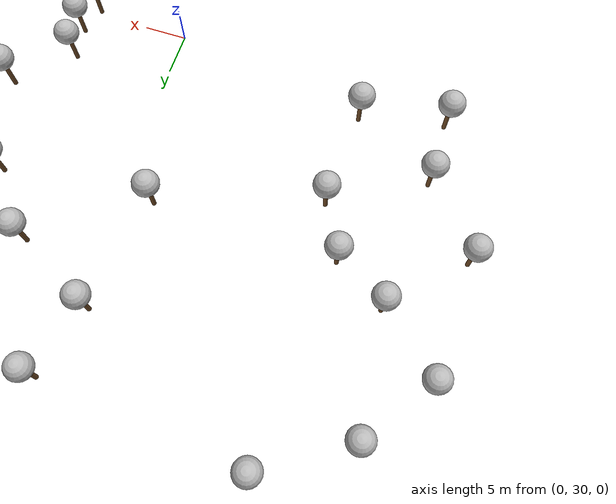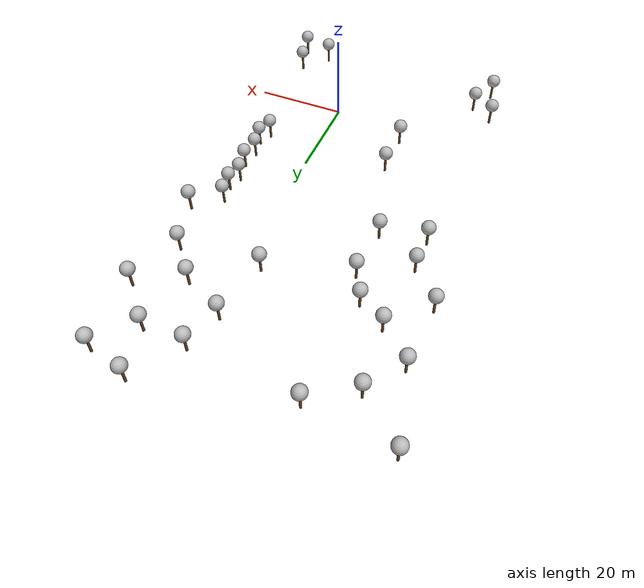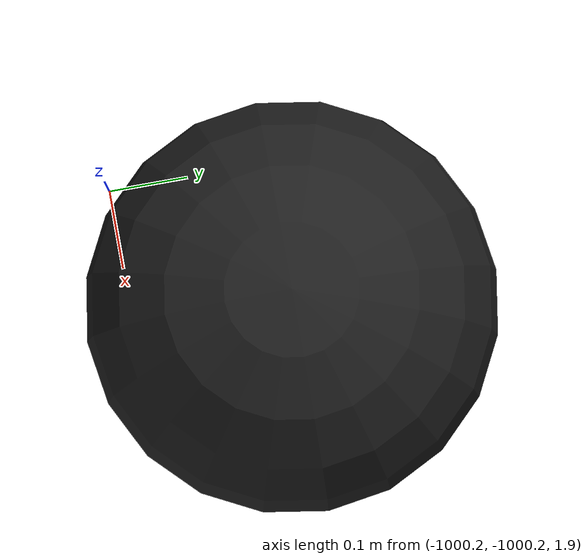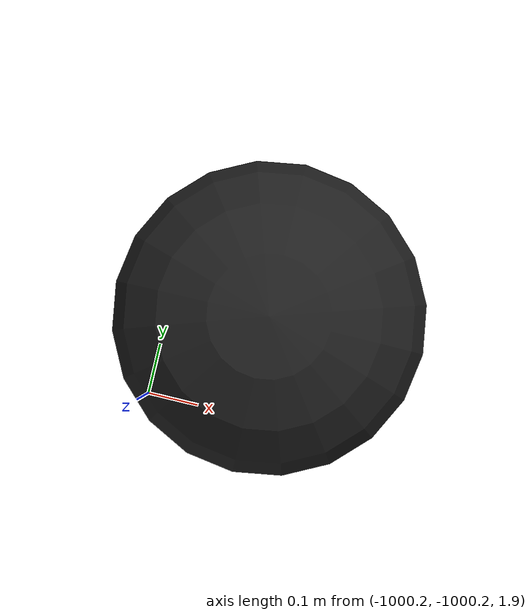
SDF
<sdf version="1.7">
 <world name="default">
  <plugin name="mrs_gazebo_static_transform_republisher_plugin" filename="libMrsGazeboCommonResources_StaticTransformRepublisher.so"/>
  <spherical_coordinates>
   <surface_model>EARTH_WGS84</surface_model>
   <latitude_deg>47.3977</latitude_deg>
   <longitude_deg>8.54559</longitude_deg>
   <elevation>0</elevation>
   <heading_deg>0</heading_deg>
  </spherical_coordinates>
  <physics name="default_physics" default="0" type="ode">
   <ode>
    <solver>
     <type>quick</type>
     <iters>10</iters>
     <sor>1.3</sor>
     <use_dynamic_moi_rescaling>0</use_dynamic_moi_rescaling>
    </solver>
    <constraints>
     <cfm>0</cfm>
     <erp>0.2</erp>
     <contact_max_correcting_vel>1000</contact_max_correcting_vel>
     <contact_surface_layer>0.001</contact_surface_layer>
    </constraints>
   </ode>
   <max_step_size>0.004</max_step_size>
   <real_time_factor>1</real_time_factor>
   <real_time_update_rate>250</real_time_update_rate>
  </physics>
  <scene><shadows>0</shadows><ambient>0.4 0.4 0.4 1</ambient><background>0.7 0.7 0.7 1</background></scene>
  <light name="sun" type="directional">
   <pose>0 0 1000 0.4 0.2 0</pose>
   <diffuse>1 1 1 1</diffuse>
   <specular>0.6 0.6 0.6 1</specular>
   <direction>0.1 0.1 -0.9</direction>
   <attenuation>
    <range>20</range>
    <constant>0.5</constant>
    <linear>0.01</linear>
    <quadratic>0.001</quadratic>
   </attenuation>
   <spot><inner_angle>0</inner_angle><outer_angle>0</outer_angle><falloff>0</falloff></spot>
  </light>
  <model name="the_void">
   <static>1</static>
   <link name="link">
    <pose>0 0 0.1 0 -0 0</pose>
    <visual name="the_void">
     <pose>0 0 2 0 -0 0</pose>
     <geometry><sphere><radius>0.25</radius></sphere></geometry>
     <material>
      <script><uri>file://media/materials/scripts/Gazebo.material</uri><name>Gazebo/Black</name></script>
     </material>
    </visual>
   </link>
   <pose>-1000 -1000 0 0 -0 0</pose>
  </model>
  <plugin name="mrs_gazebo_rviz_cam_synchronizer" filename="libMrsGazeboCommonResources_RvizCameraSynchronizer.so">
   <target_frame_id>gazebo_user_camera</target_frame_id>
   <world_origin_frame_id>uav1/gps_origin</world_origin_frame_id>
   <frame_to_follow>uav1</frame_to_follow>
  </plugin>
  <gravity>0 0 -9.8066</gravity>
  <magnetic_field>6e-06 2.3e-05 -4.2e-05</magnetic_field>
  <atmosphere type="adiabatic"/>
  <model name="tree_simple">
   <static>1</static>
   <link name="link">
    <pose>0 0 0.1 0 -0 0</pose>
    <inertial>
     <mass>666</mass>
     <inertia>
      <ixx>0.0861167</ixx>
      <ixy>0</ixy>
      <ixz>0</ixz>
      <iyy>0.0861167</iyy>
      <iyz>0</iyz>
      <izz>0.0861167</izz>
     </inertia>
    </inertial>
    <collision name="collision_trunk">
     <pose>0 0 2 0 -0 0</pose>
     <geometry><cylinder><radius>0.25</radius><length>4</length></cylinder></geometry>
     <surface>
      <contact>
       <poissons_ratio>0.347</poissons_ratio>
       <elastic_modulus>8.8e+09</elastic_modulus>
       <ode><kp>100000</kp><kd>100</kd><max_vel>100</max_vel><min_depth>0.001</min_depth></ode>
      </contact>
      <friction>
       <torsional>
        <coefficient>1</coefficient>
        <use_patch_radius>0</use_patch_radius>
        <surface_radius>0.01</surface_radius>
       </torsional>
      </friction>
     </surface>
    </collision>
    <collision name="collision_treetop">
     <pose>0 0 5.2 0 -0 0</pose>
     <geometry><sphere><radius>1.5</radius></sphere></geometry>
     <surface>
      <contact>
       <poissons_ratio>0.347</poissons_ratio>
       <elastic_modulus>8.8e+09</elastic_modulus>
       <ode><kp>100000</kp><kd>100</kd><max_vel>100</max_vel><min_depth>0.001</min_depth></ode>
      </contact>
      <friction>
       <torsional>
        <coefficient>1</coefficient>
        <use_patch_radius>0</use_patch_radius>
        <surface_radius>0.01</surface_radius>
       </torsional>
      </friction>
     </surface>
    </collision>
    <visual name="trunk">
     <pose>0 0 2 0 -0 0</pose>
     <geometry><cylinder><radius>0.25</radius><length>4</length></cylinder></geometry>
     <material>
      <script>
       <uri>model://tree_simple/scripts</uri>
       <uri>model://tree_simple/materials/textures</uri>
       <name>TreeSimple/Trunk</name>
      </script>
     </material>
    </visual>
    <visual name="treetop">
     <pose>0 0 5.2 0 -0 0</pose>
     <geometry><sphere><radius>1.5</radius></sphere></geometry>
     <material>
      <script>
       <uri>model://tree_simple/scripts</uri>
       <uri>model://tree_simple/materials/textures</uri>
       <name>TreeSimple/Treetop</name>
      </script>
     </material>
    </visual>
   </link>
   <pose>6.82311 59.8354 0 0 -0 0</pose>
  </model>
  <model name="tree_simple_0">
   <static>1</static>
   <link name="link">
    <pose>0 0 0.1 0 -0 0</pose>
    <inertial>
     <mass>666</mass>
     <inertia>
      <ixx>0.0861167</ixx>
      <ixy>0</ixy>
      <ixz>0</ixz>
      <iyy>0.0861167</iyy>
      <iyz>0</iyz>
      <izz>0.0861167</izz>
     </inertia>
    </inertial>
    <collision name="collision_trunk">
     <pose>0 0 2 0 -0 0</pose>
     <geometry><cylinder><radius>0.25</radius><length>4</length></cylinder></geometry>
     <surface>
      <contact>
       <poissons_ratio>0.347</poissons_ratio>
       <elastic_modulus>8.8e+09</elastic_modulus>
       <ode><kp>100000</kp><kd>100</kd><max_vel>100</max_vel><min_depth>0.001</min_depth></ode>
      </contact>
      <friction>
       <torsional>
        <coefficient>1</coefficient>
        <use_patch_radius>0</use_patch_radius>
        <surface_radius>0.01</surface_radius>
       </torsional>
      </friction>
     </surface>
    </collision>
    <collision name="collision_treetop">
     <pose>0 0 5.2 0 -0 0</pose>
     <geometry><sphere><radius>1.5</radius></sphere></geometry>
     <surface>
      <contact>
       <poissons_ratio>0.347</poissons_ratio>
       <elastic_modulus>8.8e+09</elastic_modulus>
       <ode><kp>100000</kp><kd>100</kd><max_vel>100</max_vel><min_depth>0.001</min_depth></ode>
      </contact>
      <friction>
       <torsional>
        <coefficient>1</coefficient>
        <use_patch_radius>0</use_patch_radius>
        <surface_radius>0.01</surface_radius>
       </torsional>
      </friction>
     </surface>
    </collision>
    <visual name="trunk">
     <pose>0 0 2 0 -0 0</pose>
     <geometry><cylinder><radius>0.25</radius><length>4</length></cylinder></geometry>
     <material>
      <script>
       <uri>model://tree_simple/scripts</uri>
       <uri>model://tree_simple/materials/textures</uri>
       <name>TreeSimple/Trunk</name>
      </script>
     </material>
    </visual>
    <visual name="treetop">
     <pose>0 0 5.2 0 -0 0</pose>
     <geometry><sphere><radius>1.5</radius></sphere></geometry>
     <material>
      <script>
       <uri>model://tree_simple/scripts</uri>
       <uri>model://tree_simple/materials/textures</uri>
       <name>TreeSimple/Treetop</name>
      </script>
     </material>
    </visual>
   </link>
   <pose>12.8669 52.9052 0 0 -0 0</pose>
  </model>
  <model name="tree_simple_0_clone">
   <static>1</static>
   <link name="link">
    <pose>0 0 0.1 0 -0 0</pose>
    <inertial>
     <mass>666</mass>
     <inertia>
      <ixx>0.0861167</ixx>
      <ixy>0</ixy>
      <ixz>0</ixz>
      <iyy>0.0861167</iyy>
      <iyz>0</iyz>
      <izz>0.0861167</izz>
     </inertia>
    </inertial>
    <collision name="collision_trunk">
     <pose>0 0 2 0 -0 0</pose>
     <geometry><cylinder><radius>0.25</radius><length>4</length></cylinder></geometry>
     <surface>
      <contact>
       <poissons_ratio>0.347</poissons_ratio>
       <elastic_modulus>8.8e+09</elastic_modulus>
       <ode><kp>100000</kp><kd>100</kd><max_vel>100</max_vel><min_depth>0.001</min_depth></ode>
      </contact>
      <friction>
       <torsional>
        <coefficient>1</coefficient>
        <use_patch_radius>0</use_patch_radius>
        <surface_radius>0.01</surface_radius>
       </torsional>
      </friction>
     </surface>
    </collision>
    <collision name="collision_treetop">
     <pose>0 0 5.2 0 -0 0</pose>
     <geometry><sphere><radius>1.5</radius></sphere></geometry>
     <surface>
      <contact>
       <poissons_ratio>0.347</poissons_ratio>
       <elastic_modulus>8.8e+09</elastic_modulus>
       <ode><kp>100000</kp><kd>100</kd><max_vel>100</max_vel><min_depth>0.001</min_depth></ode>
      </contact>
      <friction>
       <torsional>
        <coefficient>1</coefficient>
        <use_patch_radius>0</use_patch_radius>
        <surface_radius>0.01</surface_radius>
       </torsional>
      </friction>
     </surface>
    </collision>
    <visual name="trunk">
     <pose>0 0 2 0 -0 0</pose>
     <geometry><cylinder><radius>0.25</radius><length>4</length></cylinder></geometry>
     <material>
      <script>
       <uri>model://tree_simple/scripts</uri>
       <uri>model://tree_simple/materials/textures</uri>
       <name>TreeSimple/Trunk</name>
      </script>
     </material>
    </visual>
    <visual name="treetop">
     <pose>0 0 5.2 0 -0 0</pose>
     <geometry><sphere><radius>1.5</radius></sphere></geometry>
     <material>
      <script>
       <uri>model://tree_simple/scripts</uri>
       <uri>model://tree_simple/materials/textures</uri>
       <name>TreeSimple/Treetop</name>
      </script>
     </material>
    </visual>
   </link>
   <pose>16.8324 64.3347 0 0 -0 0</pose>
  </model>
  <model name="tree_simple_0_clone_0">
   <static>1</static>
   <link name="link">
    <pose>0 0 0.1 0 -0 0</pose>
    <inertial>
     <mass>666</mass>
     <inertia>
      <ixx>0.0861167</ixx>
      <ixy>0</ixy>
      <ixz>0</ixz>
      <iyy>0.0861167</iyy>
      <iyz>0</iyz>
      <izz>0.0861167</izz>
     </inertia>
    </inertial>
    <collision name="collision_trunk">
     <pose>0 0 2 0 -0 0</pose>
     <geometry><cylinder><radius>0.25</radius><length>4</length></cylinder></geometry>
     <surface>
      <contact>
       <poissons_ratio>0.347</poissons_ratio>
       <elastic_modulus>8.8e+09</elastic_modulus>
       <ode><kp>100000</kp><kd>100</kd><max_vel>100</max_vel><min_depth>0.001</min_depth></ode>
      </contact>
      <friction>
       <torsional>
        <coefficient>1</coefficient>
        <use_patch_radius>0</use_patch_radius>
        <surface_radius>0.01</surface_radius>
       </torsional>
      </friction>
     </surface>
    </collision>
    <collision name="collision_treetop">
     <pose>0 0 5.2 0 -0 0</pose>
     <geometry><sphere><radius>1.5</radius></sphere></geometry>
     <surface>
      <contact>
       <poissons_ratio>0.347</poissons_ratio>
       <elastic_modulus>8.8e+09</elastic_modulus>
       <ode><kp>100000</kp><kd>100</kd><max_vel>100</max_vel><min_depth>0.001</min_depth></ode>
      </contact>
      <friction>
       <torsional>
        <coefficient>1</coefficient>
        <use_patch_radius>0</use_patch_radius>
        <surface_radius>0.01</surface_radius>
       </torsional>
      </friction>
     </surface>
    </collision>
    <visual name="trunk">
     <pose>0 0 2 0 -0 0</pose>
     <geometry><cylinder><radius>0.25</radius><length>4</length></cylinder></geometry>
     <material>
      <script>
       <uri>model://tree_simple/scripts</uri>
       <uri>model://tree_simple/materials/textures</uri>
       <name>TreeSimple/Trunk</name>
      </script>
     </material>
    </visual>
    <visual name="treetop">
     <pose>0 0 5.2 0 -0 0</pose>
     <geometry><sphere><radius>1.5</radius></sphere></geometry>
     <material>
      <script>
       <uri>model://tree_simple/scripts</uri>
       <uri>model://tree_simple/materials/textures</uri>
       <name>TreeSimple/Treetop</name>
      </script>
     </material>
    </visual>
   </link>
   <pose>-2.64272 64.897 0 0 -0 0</pose>
  </model>
  <model name="tree_simple_0_clone_0_clone">
   <static>1</static>
   <link name="link">
    <pose>0 0 0.1 0 -0 0</pose>
    <inertial>
     <mass>666</mass>
     <inertia>
      <ixx>0.0861167</ixx>
      <ixy>0</ixy>
      <ixz>0</ixz>
      <iyy>0.0861167</iyy>
      <iyz>0</iyz>
      <izz>0.0861167</izz>
     </inertia>
    </inertial>
    <collision name="collision_trunk">
     <pose>0 0 2 0 -0 0</pose>
     <geometry><cylinder><radius>0.25</radius><length>4</length></cylinder></geometry>
     <surface>
      <contact>
       <poissons_ratio>0.347</poissons_ratio>
       <elastic_modulus>8.8e+09</elastic_modulus>
       <ode><kp>100000</kp><kd>100</kd><max_vel>100</max_vel><min_depth>0.001</min_depth></ode>
      </contact>
      <friction>
       <torsional>
        <coefficient>1</coefficient>
        <use_patch_radius>0</use_patch_radius>
        <surface_radius>0.01</surface_radius>
       </torsional>
      </friction>
     </surface>
    </collision>
    <collision name="collision_treetop">
     <pose>0 0 5.2 0 -0 0</pose>
     <geometry><sphere><radius>1.5</radius></sphere></geometry>
     <surface>
      <contact>
       <poissons_ratio>0.347</poissons_ratio>
       <elastic_modulus>8.8e+09</elastic_modulus>
       <ode><kp>100000</kp><kd>100</kd><max_vel>100</max_vel><min_depth>0.001</min_depth></ode>
      </contact>
      <friction>
       <torsional>
        <coefficient>1</coefficient>
        <use_patch_radius>0</use_patch_radius>
        <surface_radius>0.01</surface_radius>
       </torsional>
      </friction>
     </surface>
    </collision>
    <visual name="trunk">
     <pose>0 0 2 0 -0 0</pose>
     <geometry><cylinder><radius>0.25</radius><length>4</length></cylinder></geometry>
     <material>
      <script>
       <uri>model://tree_simple/scripts</uri>
       <uri>model://tree_simple/materials/textures</uri>
       <name>TreeSimple/Trunk</name>
      </script>
     </material>
    </visual>
    <visual name="treetop">
     <pose>0 0 5.2 0 -0 0</pose>
     <geometry><sphere><radius>1.5</radius></sphere></geometry>
     <material>
      <script>
       <uri>model://tree_simple/scripts</uri>
       <uri>model://tree_simple/materials/textures</uri>
       <name>TreeSimple/Treetop</name>
      </script>
     </material>
    </visual>
   </link>
   <pose>-4.6416 51.6226 0 0 -0 0</pose>
  </model>
  <model name="tree_simple_0_clone_0_clone_clone">
   <static>1</static>
   <link name="link">
    <pose>0 0 0.1 0 -0 0</pose>
    <inertial>
     <mass>666</mass>
     <inertia>
      <ixx>0.0861167</ixx>
      <ixy>0</ixy>
      <ixz>0</ixz>
      <iyy>0.0861167</iyy>
      <iyz>0</iyz>
      <izz>0.0861167</izz>
     </inertia>
    </inertial>
    <collision name="collision_trunk">
     <pose>0 0 2 0 -0 0</pose>
     <geometry><cylinder><radius>0.25</radius><length>4</length></cylinder></geometry>
     <surface>
      <contact>
       <poissons_ratio>0.347</poissons_ratio>
       <elastic_modulus>8.8e+09</elastic_modulus>
       <ode><kp>100000</kp><kd>100</kd><max_vel>100</max_vel><min_depth>0.001</min_depth></ode>
      </contact>
      <friction>
       <torsional>
        <coefficient>1</coefficient>
        <use_patch_radius>0</use_patch_radius>
        <surface_radius>0.01</surface_radius>
       </torsional>
      </friction>
     </surface>
    </collision>
    <collision name="collision_treetop">
     <pose>0 0 5.2 0 -0 0</pose>
     <geometry><sphere><radius>1.5</radius></sphere></geometry>
     <surface>
      <contact>
       <poissons_ratio>0.347</poissons_ratio>
       <elastic_modulus>8.8e+09</elastic_modulus>
       <ode><kp>100000</kp><kd>100</kd><max_vel>100</max_vel><min_depth>0.001</min_depth></ode>
      </contact>
      <friction>
       <torsional>
        <coefficient>1</coefficient>
        <use_patch_radius>0</use_patch_radius>
        <surface_radius>0.01</surface_radius>
       </torsional>
      </friction>
     </surface>
    </collision>
    <visual name="trunk">
     <pose>0 0 2 0 -0 0</pose>
     <geometry><cylinder><radius>0.25</radius><length>4</length></cylinder></geometry>
     <material>
      <script>
       <uri>model://tree_simple/scripts</uri>
       <uri>model://tree_simple/materials/textures</uri>
       <name>TreeSimple/Trunk</name>
      </script>
     </material>
    </visual>
    <visual name="treetop">
     <pose>0 0 5.2 0 -0 0</pose>
     <geometry><sphere><radius>1.5</radius></sphere></geometry>
     <material>
      <script>
       <uri>model://tree_simple/scripts</uri>
       <uri>model://tree_simple/materials/textures</uri>
       <name>TreeSimple/Treetop</name>
      </script>
     </material>
    </visual>
   </link>
   <pose>-38.4069 62.1845 0 0 -0 0</pose>
  </model>
  <model name="tree_simple_0_clone_0_clone_clone_0">
   <static>1</static>
   <link name="link">
    <pose>0 0 0.1 0 -0 0</pose>
    <inertial>
     <mass>666</mass>
     <inertia>
      <ixx>0.0861167</ixx>
      <ixy>0</ixy>
      <ixz>0</ixz>
      <iyy>0.0861167</iyy>
      <iyz>0</iyz>
      <izz>0.0861167</izz>
     </inertia>
    </inertial>
    <collision name="collision_trunk">
     <pose>0 0 2 0 -0 0</pose>
     <geometry><cylinder><radius>0.25</radius><length>4</length></cylinder></geometry>
     <surface>
      <contact>
       <poissons_ratio>0.347</poissons_ratio>
       <elastic_modulus>8.8e+09</elastic_modulus>
       <ode><kp>100000</kp><kd>100</kd><max_vel>100</max_vel><min_depth>0.001</min_depth></ode>
      </contact>
      <friction>
       <torsional>
        <coefficient>1</coefficient>
        <use_patch_radius>0</use_patch_radius>
        <surface_radius>0.01</surface_radius>
       </torsional>
      </friction>
     </surface>
    </collision>
    <collision name="collision_treetop">
     <pose>0 0 5.2 0 -0 0</pose>
     <geometry><sphere><radius>1.5</radius></sphere></geometry>
     <surface>
      <contact>
       <poissons_ratio>0.347</poissons_ratio>
       <elastic_modulus>8.8e+09</elastic_modulus>
       <ode><kp>100000</kp><kd>100</kd><max_vel>100</max_vel><min_depth>0.001</min_depth></ode>
      </contact>
      <friction>
       <torsional>
        <coefficient>1</coefficient>
        <use_patch_radius>0</use_patch_radius>
        <surface_radius>0.01</surface_radius>
       </torsional>
      </friction>
     </surface>
    </collision>
    <visual name="trunk">
     <pose>0 0 2 0 -0 0</pose>
     <geometry><cylinder><radius>0.25</radius><length>4</length></cylinder></geometry>
     <material>
      <script>
       <uri>model://tree_simple/scripts</uri>
       <uri>model://tree_simple/materials/textures</uri>
       <name>TreeSimple/Trunk</name>
      </script>
     </material>
    </visual>
    <visual name="treetop">
     <pose>0 0 5.2 0 -0 0</pose>
     <geometry><sphere><radius>1.5</radius></sphere></geometry>
     <material>
      <script>
       <uri>model://tree_simple/scripts</uri>
       <uri>model://tree_simple/materials/textures</uri>
       <name>TreeSimple/Treetop</name>
      </script>
     </material>
    </visual>
   </link>
   <pose>9.13521 72.4249 0 0 -0 0</pose>
  </model>
  <model name="tree_simple_0_clone_0_clone_clone_1">
   <static>1</static>
   <link name="link">
    <pose>0 0 0.1 0 -0 0</pose>
    <inertial>
     <mass>666</mass>
     <inertia>
      <ixx>0.0861167</ixx>
      <ixy>0</ixy>
      <ixz>0</ixz>
      <iyy>0.0861167</iyy>
      <iyz>0</iyz>
      <izz>0.0861167</izz>
     </inertia>
    </inertial>
    <collision name="collision_trunk">
     <pose>0 0 2 0 -0 0</pose>
     <geometry><cylinder><radius>0.25</radius><length>4</length></cylinder></geometry>
     <surface>
      <contact>
       <poissons_ratio>0.347</poissons_ratio>
       <elastic_modulus>8.8e+09</elastic_modulus>
       <ode><kp>100000</kp><kd>100</kd><max_vel>100</max_vel><min_depth>0.001</min_depth></ode>
      </contact>
      <friction>
       <torsional>
        <coefficient>1</coefficient>
        <use_patch_radius>0</use_patch_radius>
        <surface_radius>0.01</surface_radius>
       </torsional>
      </friction>
     </surface>
    </collision>
    <collision name="collision_treetop">
     <pose>0 0 5.2 0 -0 0</pose>
     <geometry><sphere><radius>1.5</radius></sphere></geometry>
     <surface>
      <contact>
       <poissons_ratio>0.347</poissons_ratio>
       <elastic_modulus>8.8e+09</elastic_modulus>
       <ode><kp>100000</kp><kd>100</kd><max_vel>100</max_vel><min_depth>0.001</min_depth></ode>
      </contact>
      <friction>
       <torsional>
        <coefficient>1</coefficient>
        <use_patch_radius>0</use_patch_radius>
        <surface_radius>0.01</surface_radius>
       </torsional>
      </friction>
     </surface>
    </collision>
    <visual name="trunk">
     <pose>0 0 2 0 -0 0</pose>
     <geometry><cylinder><radius>0.25</radius><length>4</length></cylinder></geometry>
     <material>
      <script>
       <uri>model://tree_simple/scripts</uri>
       <uri>model://tree_simple/materials/textures</uri>
       <name>TreeSimple/Trunk</name>
      </script>
     </material>
    </visual>
    <visual name="treetop">
     <pose>0 0 5.2 0 -0 0</pose>
     <geometry><sphere><radius>1.5</radius></sphere></geometry>
     <material>
      <script>
       <uri>model://tree_simple/scripts</uri>
       <uri>model://tree_simple/materials/textures</uri>
       <name>TreeSimple/Treetop</name>
      </script>
     </material>
    </visual>
   </link>
   <pose>16.7121 42.102 0 0 -0 0</pose>
  </model>
  <model name="tree_simple_0_clone_0_clone_clone_4">
   <static>1</static>
   <link name="link">
    <pose>0 0 0.1 0 -0 0</pose>
    <inertial>
     <mass>666</mass>
     <inertia>
      <ixx>0.0861167</ixx>
      <ixy>0</ixy>
      <ixz>0</ixz>
      <iyy>0.0861167</iyy>
      <iyz>0</iyz>
      <izz>0.0861167</izz>
     </inertia>
    </inertial>
    <collision name="collision_trunk">
     <pose>0 0 2 0 -0 0</pose>
     <geometry><cylinder><radius>0.25</radius><length>4</length></cylinder></geometry>
     <surface>
      <contact>
       <poissons_ratio>0.347</poissons_ratio>
       <elastic_modulus>8.8e+09</elastic_modulus>
       <ode><kp>100000</kp><kd>100</kd><max_vel>100</max_vel><min_depth>0.001</min_depth></ode>
      </contact>
      <friction>
       <torsional>
        <coefficient>1</coefficient>
        <use_patch_radius>0</use_patch_radius>
        <surface_radius>0.01</surface_radius>
       </torsional>
      </friction>
     </surface>
    </collision>
    <collision name="collision_treetop">
     <pose>0 0 5.2 0 -0 0</pose>
     <geometry><sphere><radius>1.5</radius></sphere></geometry>
     <surface>
      <contact>
       <poissons_ratio>0.347</poissons_ratio>
       <elastic_modulus>8.8e+09</elastic_modulus>
       <ode><kp>100000</kp><kd>100</kd><max_vel>100</max_vel><min_depth>0.001</min_depth></ode>
      </contact>
      <friction>
       <torsional>
        <coefficient>1</coefficient>
        <use_patch_radius>0</use_patch_radius>
        <surface_radius>0.01</surface_radius>
       </torsional>
      </friction>
     </surface>
    </collision>
    <visual name="trunk">
     <pose>0 0 2 0 -0 0</pose>
     <geometry><cylinder><radius>0.25</radius><length>4</length></cylinder></geometry>
     <material>
      <script>
       <uri>model://tree_simple/scripts</uri>
       <uri>model://tree_simple/materials/textures</uri>
       <name>TreeSimple/Trunk</name>
      </script>
     </material>
    </visual>
    <visual name="treetop">
     <pose>0 0 5.2 0 -0 0</pose>
     <geometry><sphere><radius>1.5</radius></sphere></geometry>
     <material>
      <script>
       <uri>model://tree_simple/scripts</uri>
       <uri>model://tree_simple/materials/textures</uri>
       <name>TreeSimple/Treetop</name>
      </script>
     </material>
    </visual>
   </link>
   <pose>15.2966 -12.9591 0 0 -0 0</pose>
  </model>
  <model name="tree_simple_0_clone_0_clone_clone_5">
   <static>1</static>
   <link name="link">
    <pose>0 0 0.1 0 -0 0</pose>
    <inertial>
     <mass>666</mass>
     <inertia>
      <ixx>0.0861167</ixx>
      <ixy>0</ixy>
      <ixz>0</ixz>
      <iyy>0.0861167</iyy>
      <iyz>0</iyz>
      <izz>0.0861167</izz>
     </inertia>
    </inertial>
    <collision name="collision_trunk">
     <pose>0 0 2 0 -0 0</pose>
     <geometry><cylinder><radius>0.25</radius><length>4</length></cylinder></geometry>
     <surface>
      <contact>
       <poissons_ratio>0.347</poissons_ratio>
       <elastic_modulus>8.8e+09</elastic_modulus>
       <ode><kp>100000</kp><kd>100</kd><max_vel>100</max_vel><min_depth>0.001</min_depth></ode>
      </contact>
      <friction>
       <torsional>
        <coefficient>1</coefficient>
        <use_patch_radius>0</use_patch_radius>
        <surface_radius>0.01</surface_radius>
       </torsional>
      </friction>
     </surface>
    </collision>
    <collision name="collision_treetop">
     <pose>0 0 5.2 0 -0 0</pose>
     <geometry><sphere><radius>1.5</radius></sphere></geometry>
     <surface>
      <contact>
       <poissons_ratio>0.347</poissons_ratio>
       <elastic_modulus>8.8e+09</elastic_modulus>
       <ode><kp>100000</kp><kd>100</kd><max_vel>100</max_vel><min_depth>0.001</min_depth></ode>
      </contact>
      <friction>
       <torsional>
        <coefficient>1</coefficient>
        <use_patch_radius>0</use_patch_radius>
        <surface_radius>0.01</surface_radius>
       </torsional>
      </friction>
     </surface>
    </collision>
    <visual name="trunk">
     <pose>0 0 2 0 -0 0</pose>
     <geometry><cylinder><radius>0.25</radius><length>4</length></cylinder></geometry>
     <material>
      <script>
       <uri>model://tree_simple/scripts</uri>
       <uri>model://tree_simple/materials/textures</uri>
       <name>TreeSimple/Trunk</name>
      </script>
     </material>
    </visual>
    <visual name="treetop">
     <pose>0 0 5.2 0 -0 0</pose>
     <geometry><sphere><radius>1.5</radius></sphere></geometry>
     <material>
      <script>
       <uri>model://tree_simple/scripts</uri>
       <uri>model://tree_simple/materials/textures</uri>
       <name>TreeSimple/Treetop</name>
      </script>
     </material>
    </visual>
   </link>
   <pose>10.4515 -18.6405 0 0 -0 0</pose>
  </model>
  <model name="tree_simple_0_clone_0_clone_clone_6">
   <static>1</static>
   <link name="link">
    <pose>0 0 0.1 0 -0 0</pose>
    <inertial>
     <mass>666</mass>
     <inertia>
      <ixx>0.0861167</ixx>
      <ixy>0</ixy>
      <ixz>0</ixz>
      <iyy>0.0861167</iyy>
      <iyz>0</iyz>
      <izz>0.0861167</izz>
     </inertia>
    </inertial>
    <collision name="collision_trunk">
     <pose>0 0 2 0 -0 0</pose>
     <geometry><cylinder><radius>0.25</radius><length>4</length></cylinder></geometry>
     <surface>
      <contact>
       <poissons_ratio>0.347</poissons_ratio>
       <elastic_modulus>8.8e+09</elastic_modulus>
       <ode><kp>100000</kp><kd>100</kd><max_vel>100</max_vel><min_depth>0.001</min_depth></ode>
      </contact>
      <friction>
       <torsional>
        <coefficient>1</coefficient>
        <use_patch_radius>0</use_patch_radius>
        <surface_radius>0.01</surface_radius>
       </torsional>
      </friction>
     </surface>
    </collision>
    <collision name="collision_treetop">
     <pose>0 0 5.2 0 -0 0</pose>
     <geometry><sphere><radius>1.5</radius></sphere></geometry>
     <surface>
      <contact>
       <poissons_ratio>0.347</poissons_ratio>
       <elastic_modulus>8.8e+09</elastic_modulus>
       <ode><kp>100000</kp><kd>100</kd><max_vel>100</max_vel><min_depth>0.001</min_depth></ode>
      </contact>
      <friction>
       <torsional>
        <coefficient>1</coefficient>
        <use_patch_radius>0</use_patch_radius>
        <surface_radius>0.01</surface_radius>
       </torsional>
      </friction>
     </surface>
    </collision>
    <visual name="trunk">
     <pose>0 0 2 0 -0 0</pose>
     <geometry><cylinder><radius>0.25</radius><length>4</length></cylinder></geometry>
     <material>
      <script>
       <uri>model://tree_simple/scripts</uri>
       <uri>model://tree_simple/materials/textures</uri>
       <name>TreeSimple/Trunk</name>
      </script>
     </material>
    </visual>
    <visual name="treetop">
     <pose>0 0 5.2 0 -0 0</pose>
     <geometry><sphere><radius>1.5</radius></sphere></geometry>
     <material>
      <script>
       <uri>model://tree_simple/scripts</uri>
       <uri>model://tree_simple/materials/textures</uri>
       <name>TreeSimple/Treetop</name>
      </script>
     </material>
    </visual>
   </link>
   <pose>16.9128 -19.7494 0 0 -0 0</pose>
  </model>
  <model name="tree_simple_0_clone_0_clone_clone_4_clone">
   <static>1</static>
   <link name="link">
    <pose>0 0 0.1 0 -0 0</pose>
    <inertial>
     <mass>666</mass>
     <inertia>
      <ixx>0.0861167</ixx>
      <ixy>0</ixy>
      <ixz>0</ixz>
      <iyy>0.0861167</iyy>
      <iyz>0</iyz>
      <izz>0.0861167</izz>
     </inertia>
    </inertial>
    <collision name="collision_trunk">
     <pose>0 0 2 0 -0 0</pose>
     <geometry><cylinder><radius>0.25</radius><length>4</length></cylinder></geometry>
     <surface>
      <contact>
       <poissons_ratio>0.347</poissons_ratio>
       <elastic_modulus>8.8e+09</elastic_modulus>
       <ode><kp>100000</kp><kd>100</kd><max_vel>100</max_vel><min_depth>0.001</min_depth></ode>
      </contact>
      <friction>
       <torsional>
        <coefficient>1</coefficient>
        <use_patch_radius>0</use_patch_radius>
        <surface_radius>0.01</surface_radius>
       </torsional>
      </friction>
     </surface>
    </collision>
    <collision name="collision_treetop">
     <pose>0 0 5.2 0 -0 0</pose>
     <geometry><sphere><radius>1.5</radius></sphere></geometry>
     <surface>
      <contact>
       <poissons_ratio>0.347</poissons_ratio>
       <elastic_modulus>8.8e+09</elastic_modulus>
       <ode><kp>100000</kp><kd>100</kd><max_vel>100</max_vel><min_depth>0.001</min_depth></ode>
      </contact>
      <friction>
       <torsional>
        <coefficient>1</coefficient>
        <use_patch_radius>0</use_patch_radius>
        <surface_radius>0.01</surface_radius>
       </torsional>
      </friction>
     </surface>
    </collision>
    <visual name="trunk">
     <pose>0 0 2 0 -0 0</pose>
     <geometry><cylinder><radius>0.25</radius><length>4</length></cylinder></geometry>
     <material>
      <script>
       <uri>model://tree_simple/scripts</uri>
       <uri>model://tree_simple/materials/textures</uri>
       <name>TreeSimple/Trunk</name>
      </script>
     </material>
    </visual>
    <visual name="treetop">
     <pose>0 0 5.2 0 -0 0</pose>
     <geometry><sphere><radius>1.5</radius></sphere></geometry>
     <material>
      <script>
       <uri>model://tree_simple/scripts</uri>
       <uri>model://tree_simple/materials/textures</uri>
       <name>TreeSimple/Treetop</name>
      </script>
     </material>
    </visual>
   </link>
   <pose>-17.55 15.2092 0 0 -0 0</pose>
  </model>
  <model name="tree_simple_0_clone_0_clone_clone_4_clone_0">
   <static>1</static>
   <link name="link">
    <pose>0 0 0.1 0 -0 0</pose>
    <inertial>
     <mass>666</mass>
     <inertia>
      <ixx>0.0861167</ixx>
      <ixy>0</ixy>
      <ixz>0</ixz>
      <iyy>0.0861167</iyy>
      <iyz>0</iyz>
      <izz>0.0861167</izz>
     </inertia>
    </inertial>
    <collision name="collision_trunk">
     <pose>0 0 2 0 -0 0</pose>
     <geometry><cylinder><radius>0.25</radius><length>4</length></cylinder></geometry>
     <surface>
      <contact>
       <poissons_ratio>0.347</poissons_ratio>
       <elastic_modulus>8.8e+09</elastic_modulus>
       <ode><kp>100000</kp><kd>100</kd><max_vel>100</max_vel><min_depth>0.001</min_depth></ode>
      </contact>
      <friction>
       <torsional>
        <coefficient>1</coefficient>
        <use_patch_radius>0</use_patch_radius>
        <surface_radius>0.01</surface_radius>
       </torsional>
      </friction>
     </surface>
    </collision>
    <collision name="collision_treetop">
     <pose>0 0 5.2 0 -0 0</pose>
     <geometry><sphere><radius>1.5</radius></sphere></geometry>
     <surface>
      <contact>
       <poissons_ratio>0.347</poissons_ratio>
       <elastic_modulus>8.8e+09</elastic_modulus>
       <ode><kp>100000</kp><kd>100</kd><max_vel>100</max_vel><min_depth>0.001</min_depth></ode>
      </contact>
      <friction>
       <torsional>
        <coefficient>1</coefficient>
        <use_patch_radius>0</use_patch_radius>
        <surface_radius>0.01</surface_radius>
       </torsional>
      </friction>
     </surface>
    </collision>
    <visual name="trunk">
     <pose>0 0 2 0 -0 0</pose>
     <geometry><cylinder><radius>0.25</radius><length>4</length></cylinder></geometry>
     <material>
      <script>
       <uri>model://tree_simple/scripts</uri>
       <uri>model://tree_simple/materials/textures</uri>
       <name>TreeSimple/Trunk</name>
      </script>
     </material>
    </visual>
    <visual name="treetop">
     <pose>0 0 5.2 0 -0 0</pose>
     <geometry><sphere><radius>1.5</radius></sphere></geometry>
     <material>
      <script>
       <uri>model://tree_simple/scripts</uri>
       <uri>model://tree_simple/materials/textures</uri>
       <name>TreeSimple/Treetop</name>
      </script>
     </material>
    </visual>
   </link>
   <pose>-17.5383 5.28827 0 0 -0 0</pose>
  </model>
  <model name="tree_simple_0_clone_0_clone_clone_2">
   <static>1</static>
   <link name="link">
    <pose>0 0 0.1 0 -0 0</pose>
    <inertial>
     <mass>666</mass>
     <inertia>
      <ixx>0.0861167</ixx>
      <ixy>0</ixy>
      <ixz>0</ixz>
      <iyy>0.0861167</iyy>
      <iyz>0</iyz>
      <izz>0.0861167</izz>
     </inertia>
    </inertial>
    <collision name="collision_trunk">
     <pose>0 0 2 0 -0 0</pose>
     <geometry><cylinder><radius>0.25</radius><length>4</length></cylinder></geometry>
     <surface>
      <contact>
       <poissons_ratio>0.347</poissons_ratio>
       <elastic_modulus>8.8e+09</elastic_modulus>
       <ode><kp>100000</kp><kd>100</kd><max_vel>100</max_vel><min_depth>0.001</min_depth></ode>
      </contact>
      <friction>
       <torsional>
        <coefficient>1</coefficient>
        <use_patch_radius>0</use_patch_radius>
        <surface_radius>0.01</surface_radius>
       </torsional>
      </friction>
     </surface>
    </collision>
    <collision name="collision_treetop">
     <pose>0 0 5.2 0 -0 0</pose>
     <geometry><sphere><radius>1.5</radius></sphere></geometry>
     <surface>
      <contact>
       <poissons_ratio>0.347</poissons_ratio>
       <elastic_modulus>8.8e+09</elastic_modulus>
       <ode><kp>100000</kp><kd>100</kd><max_vel>100</max_vel><min_depth>0.001</min_depth></ode>
      </contact>
      <friction>
       <torsional>
        <coefficient>1</coefficient>
        <use_patch_radius>0</use_patch_radius>
        <surface_radius>0.01</surface_radius>
       </torsional>
      </friction>
     </surface>
    </collision>
    <visual name="trunk">
     <pose>0 0 2 0 -0 0</pose>
     <geometry><cylinder><radius>0.25</radius><length>4</length></cylinder></geometry>
     <material>
      <script>
       <uri>model://tree_simple/scripts</uri>
       <uri>model://tree_simple/materials/textures</uri>
       <name>TreeSimple/Trunk</name>
      </script>
     </material>
    </visual>
    <visual name="treetop">
     <pose>0 0 5.2 0 -0 0</pose>
     <geometry><sphere><radius>1.5</radius></sphere></geometry>
     <material>
      <script>
       <uri>model://tree_simple/scripts</uri>
       <uri>model://tree_simple/materials/textures</uri>
       <name>TreeSimple/Treetop</name>
      </script>
     </material>
    </visual>
   </link>
   <pose>-23.2353 34.6148 0 0 -0 0</pose>
  </model>
  <model name="tree_simple_0_clone_0_clone_clone_3">
   <static>1</static>
   <link name="link">
    <pose>0 0 0.1 0 -0 0</pose>
    <inertial>
     <mass>666</mass>
     <inertia>
      <ixx>0.0861167</ixx>
      <ixy>0</ixy>
      <ixz>0</ixz>
      <iyy>0.0861167</iyy>
      <iyz>0</iyz>
      <izz>0.0861167</izz>
     </inertia>
    </inertial>
    <collision name="collision_trunk">
     <pose>0 0 2 0 -0 0</pose>
     <geometry><cylinder><radius>0.25</radius><length>4</length></cylinder></geometry>
     <surface>
      <contact>
       <poissons_ratio>0.347</poissons_ratio>
       <elastic_modulus>8.8e+09</elastic_modulus>
       <ode><kp>100000</kp><kd>100</kd><max_vel>100</max_vel><min_depth>0.001</min_depth></ode>
      </contact>
      <friction>
       <torsional>
        <coefficient>1</coefficient>
        <use_patch_radius>0</use_patch_radius>
        <surface_radius>0.01</surface_radius>
       </torsional>
      </friction>
     </surface>
    </collision>
    <collision name="collision_treetop">
     <pose>0 0 5.2 0 -0 0</pose>
     <geometry><sphere><radius>1.5</radius></sphere></geometry>
     <surface>
      <contact>
       <poissons_ratio>0.347</poissons_ratio>
       <elastic_modulus>8.8e+09</elastic_modulus>
       <ode><kp>100000</kp><kd>100</kd><max_vel>100</max_vel><min_depth>0.001</min_depth></ode>
      </contact>
      <friction>
       <torsional>
        <coefficient>1</coefficient>
        <use_patch_radius>0</use_patch_radius>
        <surface_radius>0.01</surface_radius>
       </torsional>
      </friction>
     </surface>
    </collision>
    <visual name="trunk">
     <pose>0 0 2 0 -0 0</pose>
     <geometry><cylinder><radius>0.25</radius><length>4</length></cylinder></geometry>
     <material>
      <script>
       <uri>model://tree_simple/scripts</uri>
       <uri>model://tree_simple/materials/textures</uri>
       <name>TreeSimple/Trunk</name>
      </script>
     </material>
    </visual>
    <visual name="treetop">
     <pose>0 0 5.2 0 -0 0</pose>
     <geometry><sphere><radius>1.5</radius></sphere></geometry>
     <material>
      <script>
       <uri>model://tree_simple/scripts</uri>
       <uri>model://tree_simple/materials/textures</uri>
       <name>TreeSimple/Treetop</name>
      </script>
     </material>
    </visual>
   </link>
   <pose>-22.6801 46.0382 0 0 -0 0</pose>
  </model>
  <model name="tree_simple_0_clone_0_clone_clone_7">
   <static>1</static>
   <link name="link">
    <pose>0 0 0.1 0 -0 0</pose>
    <inertial>
     <mass>666</mass>
     <inertia>
      <ixx>0.0861167</ixx>
      <ixy>0</ixy>
      <ixz>0</ixz>
      <iyy>0.0861167</iyy>
      <iyz>0</iyz>
      <izz>0.0861167</izz>
     </inertia>
    </inertial>
    <collision name="collision_trunk">
     <pose>0 0 2 0 -0 0</pose>
     <geometry><cylinder><radius>0.25</radius><length>4</length></cylinder></geometry>
     <surface>
      <contact>
       <poissons_ratio>0.347</poissons_ratio>
       <elastic_modulus>8.8e+09</elastic_modulus>
       <ode><kp>100000</kp><kd>100</kd><max_vel>100</max_vel><min_depth>0.001</min_depth></ode>
      </contact>
      <friction>
       <torsional>
        <coefficient>1</coefficient>
        <use_patch_radius>0</use_patch_radius>
        <surface_radius>0.01</surface_radius>
       </torsional>
      </friction>
     </surface>
    </collision>
    <collision name="collision_treetop">
     <pose>0 0 5.2 0 -0 0</pose>
     <geometry><sphere><radius>1.5</radius></sphere></geometry>
     <surface>
      <contact>
       <poissons_ratio>0.347</poissons_ratio>
       <elastic_modulus>8.8e+09</elastic_modulus>
       <ode><kp>100000</kp><kd>100</kd><max_vel>100</max_vel><min_depth>0.001</min_depth></ode>
      </contact>
      <friction>
       <torsional>
        <coefficient>1</coefficient>
        <use_patch_radius>0</use_patch_radius>
        <surface_radius>0.01</surface_radius>
       </torsional>
      </friction>
     </surface>
    </collision>
    <visual name="trunk">
     <pose>0 0 2 0 -0 0</pose>
     <geometry><cylinder><radius>0.25</radius><length>4</length></cylinder></geometry>
     <material>
      <script>
       <uri>model://tree_simple/scripts</uri>
       <uri>model://tree_simple/materials/textures</uri>
       <name>TreeSimple/Trunk</name>
      </script>
     </material>
    </visual>
    <visual name="treetop">
     <pose>0 0 5.2 0 -0 0</pose>
     <geometry><sphere><radius>1.5</radius></sphere></geometry>
     <material>
      <script>
       <uri>model://tree_simple/scripts</uri>
       <uri>model://tree_simple/materials/textures</uri>
       <name>TreeSimple/Treetop</name>
      </script>
     </material>
    </visual>
   </link>
   <pose>-32.8936 40.303 0 0 -0 0</pose>
  </model>
  <model name="tree_simple_0_clone_0_clone_clone_8">
   <static>1</static>
   <link name="link">
    <pose>0 0 0.1 0 -0 0</pose>
    <inertial>
     <mass>666</mass>
     <inertia>
      <ixx>0.0861167</ixx>
      <ixy>0</ixy>
      <ixz>0</ixz>
      <iyy>0.0861167</iyy>
      <iyz>0</iyz>
      <izz>0.0861167</izz>
     </inertia>
    </inertial>
    <collision name="collision_trunk">
     <pose>0 0 2 0 -0 0</pose>
     <geometry><cylinder><radius>0.25</radius><length>4</length></cylinder></geometry>
     <surface>
      <contact>
       <poissons_ratio>0.347</poissons_ratio>
       <elastic_modulus>8.8e+09</elastic_modulus>
       <ode><kp>100000</kp><kd>100</kd><max_vel>100</max_vel><min_depth>0.001</min_depth></ode>
      </contact>
      <friction>
       <torsional>
        <coefficient>1</coefficient>
        <use_patch_radius>0</use_patch_radius>
        <surface_radius>0.01</surface_radius>
       </torsional>
      </friction>
     </surface>
    </collision>
    <collision name="collision_treetop">
     <pose>0 0 5.2 0 -0 0</pose>
     <geometry><sphere><radius>1.5</radius></sphere></geometry>
     <surface>
      <contact>
       <poissons_ratio>0.347</poissons_ratio>
       <elastic_modulus>8.8e+09</elastic_modulus>
       <ode><kp>100000</kp><kd>100</kd><max_vel>100</max_vel><min_depth>0.001</min_depth></ode>
      </contact>
      <friction>
       <torsional>
        <coefficient>1</coefficient>
        <use_patch_radius>0</use_patch_radius>
        <surface_radius>0.01</surface_radius>
       </torsional>
      </friction>
     </surface>
    </collision>
    <visual name="trunk">
     <pose>0 0 2 0 -0 0</pose>
     <geometry><cylinder><radius>0.25</radius><length>4</length></cylinder></geometry>
     <material>
      <script>
       <uri>model://tree_simple/scripts</uri>
       <uri>model://tree_simple/materials/textures</uri>
       <name>TreeSimple/Trunk</name>
      </script>
     </material>
    </visual>
    <visual name="treetop">
     <pose>0 0 5.2 0 -0 0</pose>
     <geometry><sphere><radius>1.5</radius></sphere></geometry>
     <material>
      <script>
       <uri>model://tree_simple/scripts</uri>
       <uri>model://tree_simple/materials/textures</uri>
       <name>TreeSimple/Treetop</name>
      </script>
     </material>
    </visual>
   </link>
   <pose>-31.695 55.8135 0 0 -0 0</pose>
  </model>
  <model name="tree_simple_0_clone_0_clone_clone_9">
   <static>1</static>
   <link name="link">
    <pose>0 0 0.1 0 -0 0</pose>
    <inertial>
     <mass>666</mass>
     <inertia>
      <ixx>0.0861167</ixx>
      <ixy>0</ixy>
      <ixz>0</ixz>
      <iyy>0.0861167</iyy>
      <iyz>0</iyz>
      <izz>0.0861167</izz>
     </inertia>
    </inertial>
    <collision name="collision_trunk">
     <pose>0 0 2 0 -0 0</pose>
     <geometry><cylinder><radius>0.25</radius><length>4</length></cylinder></geometry>
     <surface>
      <contact>
       <poissons_ratio>0.347</poissons_ratio>
       <elastic_modulus>8.8e+09</elastic_modulus>
       <ode><kp>100000</kp><kd>100</kd><max_vel>100</max_vel><min_depth>0.001</min_depth></ode>
      </contact>
      <friction>
       <torsional>
        <coefficient>1</coefficient>
        <use_patch_radius>0</use_patch_radius>
        <surface_radius>0.01</surface_radius>
       </torsional>
      </friction>
     </surface>
    </collision>
    <collision name="collision_treetop">
     <pose>0 0 5.2 0 -0 0</pose>
     <geometry><sphere><radius>1.5</radius></sphere></geometry>
     <surface>
      <contact>
       <poissons_ratio>0.347</poissons_ratio>
       <elastic_modulus>8.8e+09</elastic_modulus>
       <ode><kp>100000</kp><kd>100</kd><max_vel>100</max_vel><min_depth>0.001</min_depth></ode>
      </contact>
      <friction>
       <torsional>
        <coefficient>1</coefficient>
        <use_patch_radius>0</use_patch_radius>
        <surface_radius>0.01</surface_radius>
       </torsional>
      </friction>
     </surface>
    </collision>
    <visual name="trunk">
     <pose>0 0 2 0 -0 0</pose>
     <geometry><cylinder><radius>0.25</radius><length>4</length></cylinder></geometry>
     <material>
      <script>
       <uri>model://tree_simple/scripts</uri>
       <uri>model://tree_simple/materials/textures</uri>
       <name>TreeSimple/Trunk</name>
      </script>
     </material>
    </visual>
    <visual name="treetop">
     <pose>0 0 5.2 0 -0 0</pose>
     <geometry><sphere><radius>1.5</radius></sphere></geometry>
     <material>
      <script>
       <uri>model://tree_simple/scripts</uri>
       <uri>model://tree_simple/materials/textures</uri>
       <name>TreeSimple/Treetop</name>
      </script>
     </material>
    </visual>
   </link>
   <pose>-0.415016 73.0445 0 0 -0 0</pose>
  </model>
  <model name="tree_simple_0_clone_0_clone_clone_10">
   <static>1</static>
   <link name="link">
    <pose>0 0 0.1 0 -0 0</pose>
    <inertial>
     <mass>666</mass>
     <inertia>
      <ixx>0.0861167</ixx>
      <ixy>0</ixy>
      <ixz>0</ixz>
      <iyy>0.0861167</iyy>
      <iyz>0</iyz>
      <izz>0.0861167</izz>
     </inertia>
    </inertial>
    <collision name="collision_trunk">
     <pose>0 0 2 0 -0 0</pose>
     <geometry><cylinder><radius>0.25</radius><length>4</length></cylinder></geometry>
     <surface>
      <contact>
       <poissons_ratio>0.347</poissons_ratio>
       <elastic_modulus>8.8e+09</elastic_modulus>
       <ode><kp>100000</kp><kd>100</kd><max_vel>100</max_vel><min_depth>0.001</min_depth></ode>
      </contact>
      <friction>
       <torsional>
        <coefficient>1</coefficient>
        <use_patch_radius>0</use_patch_radius>
        <surface_radius>0.01</surface_radius>
       </torsional>
      </friction>
     </surface>
    </collision>
    <collision name="collision_treetop">
     <pose>0 0 5.2 0 -0 0</pose>
     <geometry><sphere><radius>1.5</radius></sphere></geometry>
     <surface>
      <contact>
       <poissons_ratio>0.347</poissons_ratio>
       <elastic_modulus>8.8e+09</elastic_modulus>
       <ode><kp>100000</kp><kd>100</kd><max_vel>100</max_vel><min_depth>0.001</min_depth></ode>
      </contact>
      <friction>
       <torsional>
        <coefficient>1</coefficient>
        <use_patch_radius>0</use_patch_radius>
        <surface_radius>0.01</surface_radius>
       </torsional>
      </friction>
     </surface>
    </collision>
    <visual name="trunk">
     <pose>0 0 2 0 -0 0</pose>
     <geometry><cylinder><radius>0.25</radius><length>4</length></cylinder></geometry>
     <material>
      <script>
       <uri>model://tree_simple/scripts</uri>
       <uri>model://tree_simple/materials/textures</uri>
       <name>TreeSimple/Trunk</name>
      </script>
     </material>
    </visual>
    <visual name="treetop">
     <pose>0 0 5.2 0 -0 0</pose>
     <geometry><sphere><radius>1.5</radius></sphere></geometry>
     <material>
      <script>
       <uri>model://tree_simple/scripts</uri>
       <uri>model://tree_simple/materials/textures</uri>
       <name>TreeSimple/Treetop</name>
      </script>
     </material>
    </visual>
   </link>
   <pose>-33.0567 69.7272 0 0 -0 0</pose>
  </model>
  <model name="tree_simple_0_clone_0_clone_clone_11">
   <static>1</static>
   <link name="link">
    <pose>0 0 0.1 0 -0 0</pose>
    <inertial>
     <mass>666</mass>
     <inertia>
      <ixx>0.0861167</ixx>
      <ixy>0</ixy>
      <ixz>0</ixz>
      <iyy>0.0861167</iyy>
      <iyz>0</iyz>
      <izz>0.0861167</izz>
     </inertia>
    </inertial>
    <collision name="collision_trunk">
     <pose>0 0 2 0 -0 0</pose>
     <geometry><cylinder><radius>0.25</radius><length>4</length></cylinder></geometry>
     <surface>
      <contact>
       <poissons_ratio>0.347</poissons_ratio>
       <elastic_modulus>8.8e+09</elastic_modulus>
       <ode><kp>100000</kp><kd>100</kd><max_vel>100</max_vel><min_depth>0.001</min_depth></ode>
      </contact>
      <friction>
       <torsional>
        <coefficient>1</coefficient>
        <use_patch_radius>0</use_patch_radius>
        <surface_radius>0.01</surface_radius>
       </torsional>
      </friction>
     </surface>
    </collision>
    <collision name="collision_treetop">
     <pose>0 0 5.2 0 -0 0</pose>
     <geometry><sphere><radius>1.5</radius></sphere></geometry>
     <surface>
      <contact>
       <poissons_ratio>0.347</poissons_ratio>
       <elastic_modulus>8.8e+09</elastic_modulus>
       <ode><kp>100000</kp><kd>100</kd><max_vel>100</max_vel><min_depth>0.001</min_depth></ode>
      </contact>
      <friction>
       <torsional>
        <coefficient>1</coefficient>
        <use_patch_radius>0</use_patch_radius>
        <surface_radius>0.01</surface_radius>
       </torsional>
      </friction>
     </surface>
    </collision>
    <visual name="trunk">
     <pose>0 0 2 0 -0 0</pose>
     <geometry><cylinder><radius>0.25</radius><length>4</length></cylinder></geometry>
     <material>
      <script>
       <uri>model://tree_simple/scripts</uri>
       <uri>model://tree_simple/materials/textures</uri>
       <name>TreeSimple/Trunk</name>
      </script>
     </material>
    </visual>
    <visual name="treetop">
     <pose>0 0 5.2 0 -0 0</pose>
     <geometry><sphere><radius>1.5</radius></sphere></geometry>
     <material>
      <script>
       <uri>model://tree_simple/scripts</uri>
       <uri>model://tree_simple/materials/textures</uri>
       <name>TreeSimple/Treetop</name>
      </script>
     </material>
    </visual>
   </link>
   <pose>-24.0671 75.4676 0 0 -0 0</pose>
  </model>
  <model name="tree_simple_0_clone_0_clone_clone_12">
   <static>1</static>
   <link name="link">
    <pose>0 0 0.1 0 -0 0</pose>
    <inertial>
     <mass>666</mass>
     <inertia>
      <ixx>0.0861167</ixx>
      <ixy>0</ixy>
      <ixz>0</ixz>
      <iyy>0.0861167</iyy>
      <iyz>0</iyz>
      <izz>0.0861167</izz>
     </inertia>
    </inertial>
    <collision name="collision_trunk">
     <pose>0 0 2 0 -0 0</pose>
     <geometry><cylinder><radius>0.25</radius><length>4</length></cylinder></geometry>
     <surface>
      <contact>
       <poissons_ratio>0.347</poissons_ratio>
       <elastic_modulus>8.8e+09</elastic_modulus>
       <ode><kp>100000</kp><kd>100</kd><max_vel>100</max_vel><min_depth>0.001</min_depth></ode>
      </contact>
      <friction>
       <torsional>
        <coefficient>1</coefficient>
        <use_patch_radius>0</use_patch_radius>
        <surface_radius>0.01</surface_radius>
       </torsional>
      </friction>
     </surface>
    </collision>
    <collision name="collision_treetop">
     <pose>0 0 5.2 0 -0 0</pose>
     <geometry><sphere><radius>1.5</radius></sphere></geometry>
     <surface>
      <contact>
       <poissons_ratio>0.347</poissons_ratio>
       <elastic_modulus>8.8e+09</elastic_modulus>
       <ode><kp>100000</kp><kd>100</kd><max_vel>100</max_vel><min_depth>0.001</min_depth></ode>
      </contact>
      <friction>
       <torsional>
        <coefficient>1</coefficient>
        <use_patch_radius>0</use_patch_radius>
        <surface_radius>0.01</surface_radius>
       </torsional>
      </friction>
     </surface>
    </collision>
    <visual name="trunk">
     <pose>0 0 2 0 -0 0</pose>
     <geometry><cylinder><radius>0.25</radius><length>4</length></cylinder></geometry>
     <material>
      <script>
       <uri>model://tree_simple/scripts</uri>
       <uri>model://tree_simple/materials/textures</uri>
       <name>TreeSimple/Trunk</name>
      </script>
     </material>
    </visual>
    <visual name="treetop">
     <pose>0 0 5.2 0 -0 0</pose>
     <geometry><sphere><radius>1.5</radius></sphere></geometry>
     <material>
      <script>
       <uri>model://tree_simple/scripts</uri>
       <uri>model://tree_simple/materials/textures</uri>
       <name>TreeSimple/Treetop</name>
      </script>
     </material>
    </visual>
   </link>
   <pose>-25.7836 52.1449 0 0 -0 0</pose>
  </model>
  <model name="tree_simple_0_clone_0_clone_clone_13">
   <static>1</static>
   <link name="link">
    <pose>0 0 0.1 0 -0 0</pose>
    <inertial>
     <mass>666</mass>
     <inertia>
      <ixx>0.0861167</ixx>
      <ixy>0</ixy>
      <ixz>0</ixz>
      <iyy>0.0861167</iyy>
      <iyz>0</iyz>
      <izz>0.0861167</izz>
     </inertia>
    </inertial>
    <collision name="collision_trunk">
     <pose>0 0 2 0 -0 0</pose>
     <geometry><cylinder><radius>0.25</radius><length>4</length></cylinder></geometry>
     <surface>
      <contact>
       <poissons_ratio>0.347</poissons_ratio>
       <elastic_modulus>8.8e+09</elastic_modulus>
       <ode><kp>100000</kp><kd>100</kd><max_vel>100</max_vel><min_depth>0.001</min_depth></ode>
      </contact>
      <friction>
       <torsional>
        <coefficient>1</coefficient>
        <use_patch_radius>0</use_patch_radius>
        <surface_radius>0.01</surface_radius>
       </torsional>
      </friction>
     </surface>
    </collision>
    <collision name="collision_treetop">
     <pose>0 0 5.2 0 -0 0</pose>
     <geometry><sphere><radius>1.5</radius></sphere></geometry>
     <surface>
      <contact>
       <poissons_ratio>0.347</poissons_ratio>
       <elastic_modulus>8.8e+09</elastic_modulus>
       <ode><kp>100000</kp><kd>100</kd><max_vel>100</max_vel><min_depth>0.001</min_depth></ode>
      </contact>
      <friction>
       <torsional>
        <coefficient>1</coefficient>
        <use_patch_radius>0</use_patch_radius>
        <surface_radius>0.01</surface_radius>
       </torsional>
      </friction>
     </surface>
    </collision>
    <visual name="trunk">
     <pose>0 0 2 0 -0 0</pose>
     <geometry><cylinder><radius>0.25</radius><length>4</length></cylinder></geometry>
     <material>
      <script>
       <uri>model://tree_simple/scripts</uri>
       <uri>model://tree_simple/materials/textures</uri>
       <name>TreeSimple/Trunk</name>
      </script>
     </material>
    </visual>
    <visual name="treetop">
     <pose>0 0 5.2 0 -0 0</pose>
     <geometry><sphere><radius>1.5</radius></sphere></geometry>
     <material>
      <script>
       <uri>model://tree_simple/scripts</uri>
       <uri>model://tree_simple/materials/textures</uri>
       <name>TreeSimple/Treetop</name>
      </script>
     </material>
    </visual>
   </link>
   <pose>-32.8828 32.6016 0 0 -0 0</pose>
  </model>
  <model name="tree_simple_0_clone_0_clone_clone_11_clone">
   <static>1</static>
   <link name="link">
    <pose>0 0 0.1 0 -0 0</pose>
    <inertial>
     <mass>666</mass>
     <inertia>
      <ixx>0.0861167</ixx>
      <ixy>0</ixy>
      <ixz>0</ixz>
      <iyy>0.0861167</iyy>
      <iyz>0</iyz>
      <izz>0.0861167</izz>
     </inertia>
    </inertial>
    <collision name="collision_trunk">
     <pose>0 0 2 0 -0 0</pose>
     <geometry><cylinder><radius>0.25</radius><length>4</length></cylinder></geometry>
     <surface>
      <contact>
       <poissons_ratio>0.347</poissons_ratio>
       <elastic_modulus>8.8e+09</elastic_modulus>
       <ode><kp>100000</kp><kd>100</kd><max_vel>100</max_vel><min_depth>0.001</min_depth></ode>
      </contact>
      <friction>
       <torsional>
        <coefficient>1</coefficient>
        <use_patch_radius>0</use_patch_radius>
        <surface_radius>0.01</surface_radius>
       </torsional>
      </friction>
     </surface>
    </collision>
    <collision name="collision_treetop">
     <pose>0 0 5.2 0 -0 0</pose>
     <geometry><sphere><radius>1.5</radius></sphere></geometry>
     <surface>
      <contact>
       <poissons_ratio>0.347</poissons_ratio>
       <elastic_modulus>8.8e+09</elastic_modulus>
       <ode><kp>100000</kp><kd>100</kd><max_vel>100</max_vel><min_depth>0.001</min_depth></ode>
      </contact>
      <friction>
       <torsional>
        <coefficient>1</coefficient>
        <use_patch_radius>0</use_patch_radius>
        <surface_radius>0.01</surface_radius>
       </torsional>
      </friction>
     </surface>
    </collision>
    <visual name="trunk">
     <pose>0 0 2 0 -0 0</pose>
     <geometry><cylinder><radius>0.25</radius><length>4</length></cylinder></geometry>
     <material>
      <script>
       <uri>model://tree_simple/scripts</uri>
       <uri>model://tree_simple/materials/textures</uri>
       <name>TreeSimple/Trunk</name>
      </script>
     </material>
    </visual>
    <visual name="treetop">
     <pose>0 0 5.2 0 -0 0</pose>
     <geometry><sphere><radius>1.5</radius></sphere></geometry>
     <material>
      <script>
       <uri>model://tree_simple/scripts</uri>
       <uri>model://tree_simple/materials/textures</uri>
       <name>TreeSimple/Treetop</name>
      </script>
     </material>
    </visual>
   </link>
   <pose>-39.1964 48.1286 0 0 -0 0</pose>
  </model>
  <model name="tree_simple_0_clone_0_clone_clone_11_clone_0">
   <static>1</static>
   <link name="link">
    <pose>0 0 0.1 0 -0 0</pose>
    <inertial>
     <mass>666</mass>
     <inertia>
      <ixx>0.0861167</ixx>
      <ixy>0</ixy>
      <ixz>0</ixz>
      <iyy>0.0861167</iyy>
      <iyz>0</iyz>
      <izz>0.0861167</izz>
     </inertia>
    </inertial>
    <collision name="collision_trunk">
     <pose>0 0 2 0 -0 0</pose>
     <geometry><cylinder><radius>0.25</radius><length>4</length></cylinder></geometry>
     <surface>
      <contact>
       <poissons_ratio>0.347</poissons_ratio>
       <elastic_modulus>8.8e+09</elastic_modulus>
       <ode><kp>100000</kp><kd>100</kd><max_vel>100</max_vel><min_depth>0.001</min_depth></ode>
      </contact>
      <friction>
       <torsional>
        <coefficient>1</coefficient>
        <use_patch_radius>0</use_patch_radius>
        <surface_radius>0.01</surface_radius>
       </torsional>
      </friction>
     </surface>
    </collision>
    <collision name="collision_treetop">
     <pose>0 0 5.2 0 -0 0</pose>
     <geometry><sphere><radius>1.5</radius></sphere></geometry>
     <surface>
      <contact>
       <poissons_ratio>0.347</poissons_ratio>
       <elastic_modulus>8.8e+09</elastic_modulus>
       <ode><kp>100000</kp><kd>100</kd><max_vel>100</max_vel><min_depth>0.001</min_depth></ode>
      </contact>
      <friction>
       <torsional>
        <coefficient>1</coefficient>
        <use_patch_radius>0</use_patch_radius>
        <surface_radius>0.01</surface_radius>
       </torsional>
      </friction>
     </surface>
    </collision>
    <visual name="trunk">
     <pose>0 0 2 0 -0 0</pose>
     <geometry><cylinder><radius>0.25</radius><length>4</length></cylinder></geometry>
     <material>
      <script>
       <uri>model://tree_simple/scripts</uri>
       <uri>model://tree_simple/materials/textures</uri>
       <name>TreeSimple/Trunk</name>
      </script>
     </material>
    </visual>
    <visual name="treetop">
     <pose>0 0 5.2 0 -0 0</pose>
     <geometry><sphere><radius>1.5</radius></sphere></geometry>
     <material>
      <script>
       <uri>model://tree_simple/scripts</uri>
       <uri>model://tree_simple/materials/textures</uri>
       <name>TreeSimple/Treetop</name>
      </script>
     </material>
    </visual>
   </link>
   <pose>-42.3971 77.8902 0 0 -0 0</pose>
  </model>
  <model name="tree_simple_0_clone_0_clone_clone_11_clone_1">
   <static>1</static>
   <link name="link">
    <pose>0 0 0.1 0 -0 0</pose>
    <inertial>
     <mass>666</mass>
     <inertia>
      <ixx>0.0861167</ixx>
      <ixy>0</ixy>
      <ixz>0</ixz>
      <iyy>0.0861167</iyy>
      <iyz>0</iyz>
      <izz>0.0861167</izz>
     </inertia>
    </inertial>
    <collision name="collision_trunk">
     <pose>0 0 2 0 -0 0</pose>
     <geometry><cylinder><radius>0.25</radius><length>4</length></cylinder></geometry>
     <surface>
      <contact>
       <poissons_ratio>0.347</poissons_ratio>
       <elastic_modulus>8.8e+09</elastic_modulus>
       <ode><kp>100000</kp><kd>100</kd><max_vel>100</max_vel><min_depth>0.001</min_depth></ode>
      </contact>
      <friction>
       <torsional>
        <coefficient>1</coefficient>
        <use_patch_radius>0</use_patch_radius>
        <surface_radius>0.01</surface_radius>
       </torsional>
      </friction>
     </surface>
    </collision>
    <collision name="collision_treetop">
     <pose>0 0 5.2 0 -0 0</pose>
     <geometry><sphere><radius>1.5</radius></sphere></geometry>
     <surface>
      <contact>
       <poissons_ratio>0.347</poissons_ratio>
       <elastic_modulus>8.8e+09</elastic_modulus>
       <ode><kp>100000</kp><kd>100</kd><max_vel>100</max_vel><min_depth>0.001</min_depth></ode>
      </contact>
      <friction>
       <torsional>
        <coefficient>1</coefficient>
        <use_patch_radius>0</use_patch_radius>
        <surface_radius>0.01</surface_radius>
       </torsional>
      </friction>
     </surface>
    </collision>
    <visual name="trunk">
     <pose>0 0 2 0 -0 0</pose>
     <geometry><cylinder><radius>0.25</radius><length>4</length></cylinder></geometry>
     <material>
      <script>
       <uri>model://tree_simple/scripts</uri>
       <uri>model://tree_simple/materials/textures</uri>
       <name>TreeSimple/Trunk</name>
      </script>
     </material>
    </visual>
    <visual name="treetop">
     <pose>0 0 5.2 0 -0 0</pose>
     <geometry><sphere><radius>1.5</radius></sphere></geometry>
     <material>
      <script>
       <uri>model://tree_simple/scripts</uri>
       <uri>model://tree_simple/materials/textures</uri>
       <name>TreeSimple/Treetop</name>
      </script>
     </material>
    </visual>
   </link>
   <pose>6.31212 82.5438 0 0 -0 0</pose>
  </model>
  <model name="tree_simple_0_clone_0_clone_clone_11_clone_2">
   <static>1</static>
   <link name="link">
    <pose>0 0 0.1 0 -0 0</pose>
    <inertial>
     <mass>666</mass>
     <inertia>
      <ixx>0.0861167</ixx>
      <ixy>0</ixy>
      <ixz>0</ixz>
      <iyy>0.0861167</iyy>
      <iyz>0</iyz>
      <izz>0.0861167</izz>
     </inertia>
    </inertial>
    <collision name="collision_trunk">
     <pose>0 0 2 0 -0 0</pose>
     <geometry><cylinder><radius>0.25</radius><length>4</length></cylinder></geometry>
     <surface>
      <contact>
       <poissons_ratio>0.347</poissons_ratio>
       <elastic_modulus>8.8e+09</elastic_modulus>
       <ode><kp>100000</kp><kd>100</kd><max_vel>100</max_vel><min_depth>0.001</min_depth></ode>
      </contact>
      <friction>
       <torsional>
        <coefficient>1</coefficient>
        <use_patch_radius>0</use_patch_radius>
        <surface_radius>0.01</surface_radius>
       </torsional>
      </friction>
     </surface>
    </collision>
    <collision name="collision_treetop">
     <pose>0 0 5.2 0 -0 0</pose>
     <geometry><sphere><radius>1.5</radius></sphere></geometry>
     <surface>
      <contact>
       <poissons_ratio>0.347</poissons_ratio>
       <elastic_modulus>8.8e+09</elastic_modulus>
       <ode><kp>100000</kp><kd>100</kd><max_vel>100</max_vel><min_depth>0.001</min_depth></ode>
      </contact>
      <friction>
       <torsional>
        <coefficient>1</coefficient>
        <use_patch_radius>0</use_patch_radius>
        <surface_radius>0.01</surface_radius>
       </torsional>
      </friction>
     </surface>
    </collision>
    <visual name="trunk">
     <pose>0 0 2 0 -0 0</pose>
     <geometry><cylinder><radius>0.25</radius><length>4</length></cylinder></geometry>
     <material>
      <script>
       <uri>model://tree_simple/scripts</uri>
       <uri>model://tree_simple/materials/textures</uri>
       <name>TreeSimple/Trunk</name>
      </script>
     </material>
    </visual>
    <visual name="treetop">
     <pose>0 0 5.2 0 -0 0</pose>
     <geometry><sphere><radius>1.5</radius></sphere></geometry>
     <material>
      <script>
       <uri>model://tree_simple/scripts</uri>
       <uri>model://tree_simple/materials/textures</uri>
       <name>TreeSimple/Treetop</name>
      </script>
     </material>
    </visual>
   </link>
   <pose>15.4317 79.7817 0 0 -0 0</pose>
  </model>
  <model name="tree_simple_0_clone_0_clone_clone_1_clone">
   <static>1</static>
   <link name="link">
    <pose>0 0 0.1 0 -0 0</pose>
    <inertial>
     <mass>666</mass>
     <inertia>
      <ixx>0.0861167</ixx>
      <ixy>0</ixy>
      <ixz>0</ixz>
      <iyy>0.0861167</iyy>
      <iyz>0</iyz>
      <izz>0.0861167</izz>
     </inertia>
    </inertial>
    <collision name="collision_trunk">
     <pose>0 0 2 0 -0 0</pose>
     <geometry><cylinder><radius>0.25</radius><length>4</length></cylinder></geometry>
     <surface>
      <contact>
       <poissons_ratio>0.347</poissons_ratio>
       <elastic_modulus>8.8e+09</elastic_modulus>
       <ode><kp>100000</kp><kd>100</kd><max_vel>100</max_vel><min_depth>0.001</min_depth></ode>
      </contact>
      <friction>
       <torsional>
        <coefficient>1</coefficient>
        <use_patch_radius>0</use_patch_radius>
        <surface_radius>0.01</surface_radius>
       </torsional>
      </friction>
     </surface>
    </collision>
    <collision name="collision_treetop">
     <pose>0 0 5.2 0 -0 0</pose>
     <geometry><sphere><radius>1.5</radius></sphere></geometry>
     <surface>
      <contact>
       <poissons_ratio>0.347</poissons_ratio>
       <elastic_modulus>8.8e+09</elastic_modulus>
       <ode><kp>100000</kp><kd>100</kd><max_vel>100</max_vel><min_depth>0.001</min_depth></ode>
      </contact>
      <friction>
       <torsional>
        <coefficient>1</coefficient>
        <use_patch_radius>0</use_patch_radius>
        <surface_radius>0.01</surface_radius>
       </torsional>
      </friction>
     </surface>
    </collision>
    <visual name="trunk">
     <pose>0 0 2 0 -0 0</pose>
     <geometry><cylinder><radius>0.25</radius><length>4</length></cylinder></geometry>
     <material>
      <script>
       <uri>model://tree_simple/scripts</uri>
       <uri>model://tree_simple/materials/textures</uri>
       <name>TreeSimple/Trunk</name>
      </script>
     </material>
    </visual>
    <visual name="treetop">
     <pose>0 0 5.2 0 -0 0</pose>
     <geometry><sphere><radius>1.5</radius></sphere></geometry>
     <material>
      <script>
       <uri>model://tree_simple/scripts</uri>
       <uri>model://tree_simple/materials/textures</uri>
       <name>TreeSimple/Treetop</name>
      </script>
     </material>
    </visual>
   </link>
   <pose>13.3682 26.7498 -4.27467 0 -0 0</pose>
  </model>
  <model name="tree_simple_0_clone_0_clone_clone_1_clone_clone">
   <static>1</static>
   <link name="link">
    <pose>0 0 0.1 0 -0 0</pose>
    <inertial>
     <mass>666</mass>
     <inertia>
      <ixx>0.0861167</ixx>
      <ixy>0</ixy>
      <ixz>0</ixz>
      <iyy>0.0861167</iyy>
      <iyz>0</iyz>
      <izz>0.0861167</izz>
     </inertia>
    </inertial>
    <collision name="collision_trunk">
     <pose>0 0 2 0 -0 0</pose>
     <geometry><cylinder><radius>0.25</radius><length>4</length></cylinder></geometry>
     <surface>
      <contact>
       <poissons_ratio>0.347</poissons_ratio>
       <elastic_modulus>8.8e+09</elastic_modulus>
       <ode><kp>100000</kp><kd>100</kd><max_vel>100</max_vel><min_depth>0.001</min_depth></ode>
      </contact>
      <friction>
       <torsional>
        <coefficient>1</coefficient>
        <use_patch_radius>0</use_patch_radius>
        <surface_radius>0.01</surface_radius>
       </torsional>
      </friction>
     </surface>
    </collision>
    <collision name="collision_treetop">
     <pose>0 0 5.2 0 -0 0</pose>
     <geometry><sphere><radius>1.5</radius></sphere></geometry>
     <surface>
      <contact>
       <poissons_ratio>0.347</poissons_ratio>
       <elastic_modulus>8.8e+09</elastic_modulus>
       <ode><kp>100000</kp><kd>100</kd><max_vel>100</max_vel><min_depth>0.001</min_depth></ode>
      </contact>
      <friction>
       <torsional>
        <coefficient>1</coefficient>
        <use_patch_radius>0</use_patch_radius>
        <surface_radius>0.01</surface_radius>
       </torsional>
      </friction>
     </surface>
    </collision>
    <visual name="trunk">
     <pose>0 0 2 0 -0 0</pose>
     <geometry><cylinder><radius>0.25</radius><length>4</length></cylinder></geometry>
     <material>
      <script>
       <uri>model://tree_simple/scripts</uri>
       <uri>model://tree_simple/materials/textures</uri>
       <name>TreeSimple/Trunk</name>
      </script>
     </material>
    </visual>
    <visual name="treetop">
     <pose>0 0 5.2 0 -0 0</pose>
     <geometry><sphere><radius>1.5</radius></sphere></geometry>
     <material>
      <script>
       <uri>model://tree_simple/scripts</uri>
       <uri>model://tree_simple/materials/textures</uri>
       <name>TreeSimple/Treetop</name>
      </script>
     </material>
    </visual>
   </link>
   <pose>14.4464 29.8971 -4.7457 0 -0 0</pose>
  </model>
  <model name="tree_simple_0_clone_0_clone_clone_1_clone_clone_0">
   <static>1</static>
   <link name="link">
    <pose>0 0 0.1 0 -0 0</pose>
    <inertial>
     <mass>666</mass>
     <inertia>
      <ixx>0.0861167</ixx>
      <ixy>0</ixy>
      <ixz>0</ixz>
      <iyy>0.0861167</iyy>
      <iyz>0</iyz>
      <izz>0.0861167</izz>
     </inertia>
    </inertial>
    <collision name="collision_trunk">
     <pose>0 0 2 0 -0 0</pose>
     <geometry><cylinder><radius>0.25</radius><length>4</length></cylinder></geometry>
     <surface>
      <contact>
       <poissons_ratio>0.347</poissons_ratio>
       <elastic_modulus>8.8e+09</elastic_modulus>
       <ode><kp>100000</kp><kd>100</kd><max_vel>100</max_vel><min_depth>0.001</min_depth></ode>
      </contact>
      <friction>
       <torsional>
        <coefficient>1</coefficient>
        <use_patch_radius>0</use_patch_radius>
        <surface_radius>0.01</surface_radius>
       </torsional>
      </friction>
     </surface>
    </collision>
    <collision name="collision_treetop">
     <pose>0 0 5.2 0 -0 0</pose>
     <geometry><sphere><radius>1.5</radius></sphere></geometry>
     <surface>
      <contact>
       <poissons_ratio>0.347</poissons_ratio>
       <elastic_modulus>8.8e+09</elastic_modulus>
       <ode><kp>100000</kp><kd>100</kd><max_vel>100</max_vel><min_depth>0.001</min_depth></ode>
      </contact>
      <friction>
       <torsional>
        <coefficient>1</coefficient>
        <use_patch_radius>0</use_patch_radius>
        <surface_radius>0.01</surface_radius>
       </torsional>
      </friction>
     </surface>
    </collision>
    <visual name="trunk">
     <pose>0 0 2 0 -0 0</pose>
     <geometry><cylinder><radius>0.25</radius><length>4</length></cylinder></geometry>
     <material>
      <script>
       <uri>model://tree_simple/scripts</uri>
       <uri>model://tree_simple/materials/textures</uri>
       <name>TreeSimple/Trunk</name>
      </script>
     </material>
    </visual>
    <visual name="treetop">
     <pose>0 0 5.2 0 -0 0</pose>
     <geometry><sphere><radius>1.5</radius></sphere></geometry>
     <material>
      <script>
       <uri>model://tree_simple/scripts</uri>
       <uri>model://tree_simple/materials/textures</uri>
       <name>TreeSimple/Treetop</name>
      </script>
     </material>
    </visual>
   </link>
   <pose>13.8006 33.8613 -4.7457 0 -0 0</pose>
  </model>
  <model name="tree_simple_0_clone_0_clone_clone_1_clone_clone_1">
   <static>1</static>
   <link name="link">
    <pose>0 0 0.1 0 -0 0</pose>
    <inertial>
     <mass>666</mass>
     <inertia>
      <ixx>0.0861167</ixx>
      <ixy>0</ixy>
      <ixz>0</ixz>
      <iyy>0.0861167</iyy>
      <iyz>0</iyz>
      <izz>0.0861167</izz>
     </inertia>
    </inertial>
    <collision name="collision_trunk">
     <pose>0 0 2 0 -0 0</pose>
     <geometry><cylinder><radius>0.25</radius><length>4</length></cylinder></geometry>
     <surface>
      <contact>
       <poissons_ratio>0.347</poissons_ratio>
       <elastic_modulus>8.8e+09</elastic_modulus>
       <ode><kp>100000</kp><kd>100</kd><max_vel>100</max_vel><min_depth>0.001</min_depth></ode>
      </contact>
      <friction>
       <torsional>
        <coefficient>1</coefficient>
        <use_patch_radius>0</use_patch_radius>
        <surface_radius>0.01</surface_radius>
       </torsional>
      </friction>
     </surface>
    </collision>
    <collision name="collision_treetop">
     <pose>0 0 5.2 0 -0 0</pose>
     <geometry><sphere><radius>1.5</radius></sphere></geometry>
     <surface>
      <contact>
       <poissons_ratio>0.347</poissons_ratio>
       <elastic_modulus>8.8e+09</elastic_modulus>
       <ode><kp>100000</kp><kd>100</kd><max_vel>100</max_vel><min_depth>0.001</min_depth></ode>
      </contact>
      <friction>
       <torsional>
        <coefficient>1</coefficient>
        <use_patch_radius>0</use_patch_radius>
        <surface_radius>0.01</surface_radius>
       </torsional>
      </friction>
     </surface>
    </collision>
    <visual name="trunk">
     <pose>0 0 2 0 -0 0</pose>
     <geometry><cylinder><radius>0.25</radius><length>4</length></cylinder></geometry>
     <material>
      <script>
       <uri>model://tree_simple/scripts</uri>
       <uri>model://tree_simple/materials/textures</uri>
       <name>TreeSimple/Trunk</name>
      </script>
     </material>
    </visual>
    <visual name="treetop">
     <pose>0 0 5.2 0 -0 0</pose>
     <geometry><sphere><radius>1.5</radius></sphere></geometry>
     <material>
      <script>
       <uri>model://tree_simple/scripts</uri>
       <uri>model://tree_simple/materials/textures</uri>
       <name>TreeSimple/Treetop</name>
      </script>
     </material>
    </visual>
   </link>
   <pose>14.4798 22.0908 -4.27467 0 -0 0</pose>
  </model>
  <model name="tree_simple_0_clone_0_clone_clone_1_clone_clone_2">
   <static>1</static>
   <link name="link">
    <pose>0 0 0.1 0 -0 0</pose>
    <inertial>
     <mass>666</mass>
     <inertia>
      <ixx>0.0861167</ixx>
      <ixy>0</ixy>
      <ixz>0</ixz>
      <iyy>0.0861167</iyy>
      <iyz>0</iyz>
      <izz>0.0861167</izz>
     </inertia>
    </inertial>
    <collision name="collision_trunk">
     <pose>0 0 2 0 -0 0</pose>
     <geometry><cylinder><radius>0.25</radius><length>4</length></cylinder></geometry>
     <surface>
      <contact>
       <poissons_ratio>0.347</poissons_ratio>
       <elastic_modulus>8.8e+09</elastic_modulus>
       <ode><kp>100000</kp><kd>100</kd><max_vel>100</max_vel><min_depth>0.001</min_depth></ode>
      </contact>
      <friction>
       <torsional>
        <coefficient>1</coefficient>
        <use_patch_radius>0</use_patch_radius>
        <surface_radius>0.01</surface_radius>
       </torsional>
      </friction>
     </surface>
    </collision>
    <collision name="collision_treetop">
     <pose>0 0 5.2 0 -0 0</pose>
     <geometry><sphere><radius>1.5</radius></sphere></geometry>
     <surface>
      <contact>
       <poissons_ratio>0.347</poissons_ratio>
       <elastic_modulus>8.8e+09</elastic_modulus>
       <ode><kp>100000</kp><kd>100</kd><max_vel>100</max_vel><min_depth>0.001</min_depth></ode>
      </contact>
      <friction>
       <torsional>
        <coefficient>1</coefficient>
        <use_patch_radius>0</use_patch_radius>
        <surface_radius>0.01</surface_radius>
       </torsional>
      </friction>
     </surface>
    </collision>
    <visual name="trunk">
     <pose>0 0 2 0 -0 0</pose>
     <geometry><cylinder><radius>0.25</radius><length>4</length></cylinder></geometry>
     <material>
      <script>
       <uri>model://tree_simple/scripts</uri>
       <uri>model://tree_simple/materials/textures</uri>
       <name>TreeSimple/Trunk</name>
      </script>
     </material>
    </visual>
    <visual name="treetop">
     <pose>0 0 5.2 0 -0 0</pose>
     <geometry><sphere><radius>1.5</radius></sphere></geometry>
     <material>
      <script>
       <uri>model://tree_simple/scripts</uri>
       <uri>model://tree_simple/materials/textures</uri>
       <name>TreeSimple/Treetop</name>
      </script>
     </material>
    </visual>
   </link>
   <pose>13.9771 17.7579 -4.27467 0 -0 0</pose>
  </model>
  <model name="tree_simple_0_clone_0_clone_clone_1_clone_clone_4">
   <static>1</static>
   <link name="link">
    <pose>0 0 0.1 0 -0 0</pose>
    <inertial>
     <mass>666</mass>
     <inertia>
      <ixx>0.0861167</ixx>
      <ixy>0</ixy>
      <ixz>0</ixz>
      <iyy>0.0861167</iyy>
      <iyz>0</iyz>
      <izz>0.0861167</izz>
     </inertia>
    </inertial>
    <collision name="collision_trunk">
     <pose>0 0 2 0 -0 0</pose>
     <geometry><cylinder><radius>0.25</radius><length>4</length></cylinder></geometry>
     <surface>
      <contact>
       <poissons_ratio>0.347</poissons_ratio>
       <elastic_modulus>8.8e+09</elastic_modulus>
       <ode><kp>100000</kp><kd>100</kd><max_vel>100</max_vel><min_depth>0.001</min_depth></ode>
      </contact>
      <friction>
       <torsional>
        <coefficient>1</coefficient>
        <use_patch_radius>0</use_patch_radius>
        <surface_radius>0.01</surface_radius>
       </torsional>
      </friction>
     </surface>
    </collision>
    <collision name="collision_treetop">
     <pose>0 0 5.2 0 -0 0</pose>
     <geometry><sphere><radius>1.5</radius></sphere></geometry>
     <surface>
      <contact>
       <poissons_ratio>0.347</poissons_ratio>
       <elastic_modulus>8.8e+09</elastic_modulus>
       <ode><kp>100000</kp><kd>100</kd><max_vel>100</max_vel><min_depth>0.001</min_depth></ode>
      </contact>
      <friction>
       <torsional>
        <coefficient>1</coefficient>
        <use_patch_radius>0</use_patch_radius>
        <surface_radius>0.01</surface_radius>
       </torsional>
      </friction>
     </surface>
    </collision>
    <visual name="trunk">
     <pose>0 0 2 0 -0 0</pose>
     <geometry><cylinder><radius>0.25</radius><length>4</length></cylinder></geometry>
     <material>
      <script>
       <uri>model://tree_simple/scripts</uri>
       <uri>model://tree_simple/materials/textures</uri>
       <name>TreeSimple/Trunk</name>
      </script>
     </material>
    </visual>
    <visual name="treetop">
     <pose>0 0 5.2 0 -0 0</pose>
     <geometry><sphere><radius>1.5</radius></sphere></geometry>
     <material>
      <script>
       <uri>model://tree_simple/scripts</uri>
       <uri>model://tree_simple/materials/textures</uri>
       <name>TreeSimple/Treetop</name>
      </script>
     </material>
    </visual>
   </link>
   <pose>14.8506 13.6404 -4.27467 0 -0 0</pose>
  </model>
  <model name="tree_simple_0_clone_0_clone_clone_1_clone_clone_5">
   <static>1</static>
   <link name="link">
    <pose>0 0 0.1 0 -0 0</pose>
    <inertial>
     <mass>666</mass>
     <inertia>
      <ixx>0.0861167</ixx>
      <ixy>0</ixy>
      <ixz>0</ixz>
      <iyy>0.0861167</iyy>
      <iyz>0</iyz>
      <izz>0.0861167</izz>
     </inertia>
    </inertial>
    <collision name="collision_trunk">
     <pose>0 0 2 0 -0 0</pose>
     <geometry><cylinder><radius>0.25</radius><length>4</length></cylinder></geometry>
     <surface>
      <contact>
       <poissons_ratio>0.347</poissons_ratio>
       <elastic_modulus>8.8e+09</elastic_modulus>
       <ode><kp>100000</kp><kd>100</kd><max_vel>100</max_vel><min_depth>0.001</min_depth></ode>
      </contact>
      <friction>
       <torsional>
        <coefficient>1</coefficient>
        <use_patch_radius>0</use_patch_radius>
        <surface_radius>0.01</surface_radius>
       </torsional>
      </friction>
     </surface>
    </collision>
    <collision name="collision_treetop">
     <pose>0 0 5.2 0 -0 0</pose>
     <geometry><sphere><radius>1.5</radius></sphere></geometry>
     <surface>
      <contact>
       <poissons_ratio>0.347</poissons_ratio>
       <elastic_modulus>8.8e+09</elastic_modulus>
       <ode><kp>100000</kp><kd>100</kd><max_vel>100</max_vel><min_depth>0.001</min_depth></ode>
      </contact>
      <friction>
       <torsional>
        <coefficient>1</coefficient>
        <use_patch_radius>0</use_patch_radius>
        <surface_radius>0.01</surface_radius>
       </torsional>
      </friction>
     </surface>
    </collision>
    <visual name="trunk">
     <pose>0 0 2 0 -0 0</pose>
     <geometry><cylinder><radius>0.25</radius><length>4</length></cylinder></geometry>
     <material>
      <script>
       <uri>model://tree_simple/scripts</uri>
       <uri>model://tree_simple/materials/textures</uri>
       <name>TreeSimple/Trunk</name>
      </script>
     </material>
    </visual>
    <visual name="treetop">
     <pose>0 0 5.2 0 -0 0</pose>
     <geometry><sphere><radius>1.5</radius></sphere></geometry>
     <material>
      <script>
       <uri>model://tree_simple/scripts</uri>
       <uri>model://tree_simple/materials/textures</uri>
       <name>TreeSimple/Treetop</name>
      </script>
     </material>
    </visual>
   </link>
   <pose>13.6256 10.3609 -4.27467 0 -0 0</pose>
  </model>
  <model name="tree_simple_0_clone_0_clone_clone_4_clone_0_clone">
   <static>1</static>
   <link name="link">
    <pose>0 0 0.1 0 -0 0</pose>
    <inertial>
     <mass>666</mass>
     <inertia>
      <ixx>0.0861167</ixx>
      <ixy>0</ixy>
      <ixz>0</ixz>
      <iyy>0.0861167</iyy>
      <iyz>0</iyz>
      <izz>0.0861167</izz>
     </inertia>
    </inertial>
    <collision name="collision_trunk">
     <pose>0 0 2 0 -0 0</pose>
     <geometry><cylinder><radius>0.25</radius><length>4</length></cylinder></geometry>
     <surface>
      <contact>
       <poissons_ratio>0.347</poissons_ratio>
       <elastic_modulus>8.8e+09</elastic_modulus>
       <ode><kp>100000</kp><kd>100</kd><max_vel>100</max_vel><min_depth>0.001</min_depth></ode>
      </contact>
      <friction>
       <torsional>
        <coefficient>1</coefficient>
        <use_patch_radius>0</use_patch_radius>
        <surface_radius>0.01</surface_radius>
       </torsional>
      </friction>
     </surface>
    </collision>
    <collision name="collision_treetop">
     <pose>0 0 5.2 0 -0 0</pose>
     <geometry><sphere><radius>1.5</radius></sphere></geometry>
     <surface>
      <contact>
       <poissons_ratio>0.347</poissons_ratio>
       <elastic_modulus>8.8e+09</elastic_modulus>
       <ode><kp>100000</kp><kd>100</kd><max_vel>100</max_vel><min_depth>0.001</min_depth></ode>
      </contact>
      <friction>
       <torsional>
        <coefficient>1</coefficient>
        <use_patch_radius>0</use_patch_radius>
        <surface_radius>0.01</surface_radius>
       </torsional>
      </friction>
     </surface>
    </collision>
    <visual name="trunk">
     <pose>0 0 2 0 -0 0</pose>
     <geometry><cylinder><radius>0.25</radius><length>4</length></cylinder></geometry>
     <material>
      <script>
       <uri>model://tree_simple/scripts</uri>
       <uri>model://tree_simple/materials/textures</uri>
       <name>TreeSimple/Trunk</name>
      </script>
     </material>
    </visual>
    <visual name="treetop">
     <pose>0 0 5.2 0 -0 0</pose>
     <geometry><sphere><radius>1.5</radius></sphere></geometry>
     <material>
      <script>
       <uri>model://tree_simple/scripts</uri>
       <uri>model://tree_simple/materials/textures</uri>
       <name>TreeSimple/Treetop</name>
      </script>
     </material>
    </visual>
   </link>
   <pose>-33.1265 -19.5171 0 0 -0 0</pose>
  </model>
  <model name="tree_simple_0_clone_0_clone_clone_4_clone_0_clone_0">
   <static>1</static>
   <link name="link">
    <pose>0 0 0.1 0 -0 0</pose>
    <inertial>
     <mass>666</mass>
     <inertia>
      <ixx>0.0861167</ixx>
      <ixy>0</ixy>
      <ixz>0</ixz>
      <iyy>0.0861167</iyy>
      <iyz>0</iyz>
      <izz>0.0861167</izz>
     </inertia>
    </inertial>
    <collision name="collision_trunk">
     <pose>0 0 2 0 -0 0</pose>
     <geometry><cylinder><radius>0.25</radius><length>4</length></cylinder></geometry>
     <surface>
      <contact>
       <poissons_ratio>0.347</poissons_ratio>
       <elastic_modulus>8.8e+09</elastic_modulus>
       <ode><kp>100000</kp><kd>100</kd><max_vel>100</max_vel><min_depth>0.001</min_depth></ode>
      </contact>
      <friction>
       <torsional>
        <coefficient>1</coefficient>
        <use_patch_radius>0</use_patch_radius>
        <surface_radius>0.01</surface_radius>
       </torsional>
      </friction>
     </surface>
    </collision>
    <collision name="collision_treetop">
     <pose>0 0 5.2 0 -0 0</pose>
     <geometry><sphere><radius>1.5</radius></sphere></geometry>
     <surface>
      <contact>
       <poissons_ratio>0.347</poissons_ratio>
       <elastic_modulus>8.8e+09</elastic_modulus>
       <ode><kp>100000</kp><kd>100</kd><max_vel>100</max_vel><min_depth>0.001</min_depth></ode>
      </contact>
      <friction>
       <torsional>
        <coefficient>1</coefficient>
        <use_patch_radius>0</use_patch_radius>
        <surface_radius>0.01</surface_radius>
       </torsional>
      </friction>
     </surface>
    </collision>
    <visual name="trunk">
     <pose>0 0 2 0 -0 0</pose>
     <geometry><cylinder><radius>0.25</radius><length>4</length></cylinder></geometry>
     <material>
      <script>
       <uri>model://tree_simple/scripts</uri>
       <uri>model://tree_simple/materials/textures</uri>
       <name>TreeSimple/Trunk</name>
      </script>
     </material>
    </visual>
    <visual name="treetop">
     <pose>0 0 5.2 0 -0 0</pose>
     <geometry><sphere><radius>1.5</radius></sphere></geometry>
     <material>
      <script>
       <uri>model://tree_simple/scripts</uri>
       <uri>model://tree_simple/materials/textures</uri>
       <name>TreeSimple/Treetop</name>
      </script>
     </material>
    </visual>
   </link>
   <pose>-30.2974 -13.1155 0 0 -0 0</pose>
  </model>
  <model name="tree_simple_0_clone_0_clone_clone_4_clone_0_clone_1">
   <static>1</static>
   <link name="link">
    <pose>0 0 0.1 0 -0 0</pose>
    <inertial>
     <mass>666</mass>
     <inertia>
      <ixx>0.0861167</ixx>
      <ixy>0</ixy>
      <ixz>0</ixz>
      <iyy>0.0861167</iyy>
      <iyz>0</iyz>
      <izz>0.0861167</izz>
     </inertia>
    </inertial>
    <collision name="collision_trunk">
     <pose>0 0 2 0 -0 0</pose>
     <geometry><cylinder><radius>0.25</radius><length>4</length></cylinder></geometry>
     <surface>
      <contact>
       <poissons_ratio>0.347</poissons_ratio>
       <elastic_modulus>8.8e+09</elastic_modulus>
       <ode><kp>100000</kp><kd>100</kd><max_vel>100</max_vel><min_depth>0.001</min_depth></ode>
      </contact>
      <friction>
       <torsional>
        <coefficient>1</coefficient>
        <use_patch_radius>0</use_patch_radius>
        <surface_radius>0.01</surface_radius>
       </torsional>
      </friction>
     </surface>
    </collision>
    <collision name="collision_treetop">
     <pose>0 0 5.2 0 -0 0</pose>
     <geometry><sphere><radius>1.5</radius></sphere></geometry>
     <surface>
      <contact>
       <poissons_ratio>0.347</poissons_ratio>
       <elastic_modulus>8.8e+09</elastic_modulus>
       <ode><kp>100000</kp><kd>100</kd><max_vel>100</max_vel><min_depth>0.001</min_depth></ode>
      </contact>
      <friction>
       <torsional>
        <coefficient>1</coefficient>
        <use_patch_radius>0</use_patch_radius>
        <surface_radius>0.01</surface_radius>
       </torsional>
      </friction>
     </surface>
    </collision>
    <visual name="trunk">
     <pose>0 0 2 0 -0 0</pose>
     <geometry><cylinder><radius>0.25</radius><length>4</length></cylinder></geometry>
     <material>
      <script>
       <uri>model://tree_simple/scripts</uri>
       <uri>model://tree_simple/materials/textures</uri>
       <name>TreeSimple/Trunk</name>
      </script>
     </material>
    </visual>
    <visual name="treetop">
     <pose>0 0 5.2 0 -0 0</pose>
     <geometry><sphere><radius>1.5</radius></sphere></geometry>
     <material>
      <script>
       <uri>model://tree_simple/scripts</uri>
       <uri>model://tree_simple/materials/textures</uri>
       <name>TreeSimple/Treetop</name>
      </script>
     </material>
    </visual>
   </link>
   <pose>-35.1084 -10.0287 0 0 -0 0</pose>
  </model>
 </world>
</sdf>
